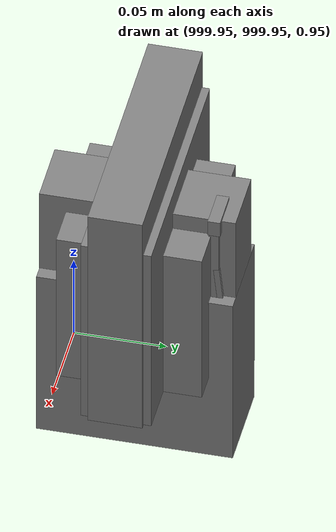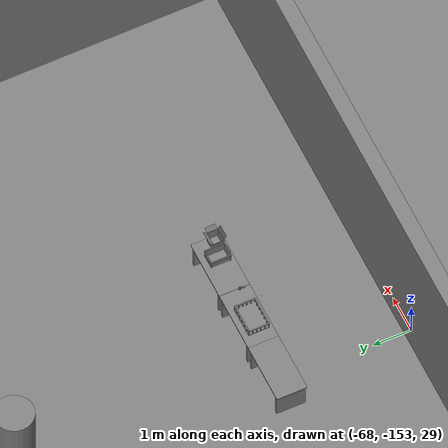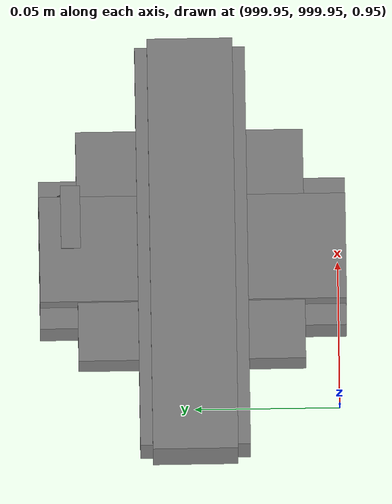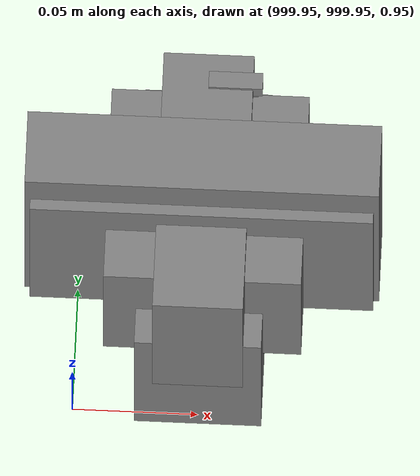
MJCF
<mujoco>
    <option gravity="0.000000000 0.000000000 -9.810000420" timestep="0.0049999999" integrator="implicitfast" density="1.225" viscosity="1.8000001e-05" noslip_iterations="10" iterations="100" sdf_iterations="50">
        <flag multiccd="disable"/>
    </option>
    <size memory="1000M"/>
    <compiler coordinate="local"/>
    <worldbody>
        <light cutoff="30" pos="0 1 1" dir="0 -1 -2"/>
        <light cutoff="30" pos="0 -1 1" dir="0 1 -2"/>
        <body pos="-64.866622925 -149.383972168 30.183746338" euler="89.999984741 89.999946594 0.000000000" name="openloong_gripper_2f85_fix_base_usda_bluebox_01">
            <geom contype="1" conaffinity="1" density="1000" type="box" material="" rgba="0.500000000 0.500000000 0.500000000 1.000000000" solimp="0.899999976 0.949999988 0.001000000" friction="1.000000000 0.005000000 0.000100000" solref="0.020000000 1.000000000" margin="0" condim="3" group="0" pos="0.276580811 0.187225342 0.000068665" quat="0.707106948 0.000077471 0.707106352 0.000077486" size="0.100000001 0.057999998 0.010000000" name="openloong_gripper_2f85_fix_base_usda_geom_40D1EACD_513C_476E_AEEA_4DF667C75590"/>
            <geom contype="1" conaffinity="1" density="1000" type="box" material="" rgba="0.500000000 0.500000000 0.500000000 1.000000000" solimp="0.899999976 0.949999988 0.001000000" friction="1.000000000 0.005000000 0.000100000" solref="0.020000000 1.000000000" margin="0" condim="3" group="0" pos="0.000000000 0.002883911 0.000000000" quat="0.999999881 0.000000000 0.000000000 0.000000000" size="0.254000008 0.003000000 0.172000006" name="openloong_gripper_2f85_fix_base_usda_geom_1A50C2B7_493B_40DB_BC93_6E1B12433A99"/>
            <geom contype="1" conaffinity="1" density="1000" type="box" material="" rgba="0.500000000 0.500000000 0.500000000 1.000000000" solimp="0.899999976 0.949999988 0.001000000" friction="1.000000000 0.005000000 0.000100000" solref="0.020000000 1.000000000" margin="0" condim="3" group="0" pos="0.000000000 0.124874115 0.173484802" quat="0.999796331 0.020176515 -0.000000015 0.000000030" size="0.259999990 0.119999997 0.007000000" name="openloong_gripper_2f85_fix_base_usda_geom_1E1AD202_FDF4_4715_B5D5_B31E4A72B23F"/>
            <geom contype="1" conaffinity="1" density="1000" type="box" material="" rgba="0.500000000 0.500000000 0.500000000 1.000000000" solimp="0.899999976 0.949999988 0.001000000" friction="1.000000000 0.005000000 0.000100000" solref="0.020000000 1.000000000" margin="0" condim="3" group="0" pos="0.000000000 0.124874115 -0.173469543" quat="0.999796331 -0.020176545 -0.000000015 0.000000000" size="0.259999990 0.119999997 0.007000000" name="openloong_gripper_2f85_fix_base_usda_geom_BDC14CC6_F6CB_40ED_ABED_118E5F71A2EF"/>
            <geom contype="1" conaffinity="1" density="1000" type="box" material="" rgba="0.500000000 0.500000000 0.500000000 1.000000000" solimp="0.899999976 0.949999988 0.001000000" friction="1.000000000 0.005000000 0.000100000" solref="0.020000000 1.000000000" margin="0" condim="3" group="0" pos="0.000000000 0.214008331 0.188980103" quat="0.999912977 0.013176724 0.000000015 0.000000000" size="0.259999990 0.029999999 0.012500000" name="openloong_gripper_2f85_fix_base_usda_geom_EA6DC2A7_AAAD_45DF_B12F_FDB9B66CD8E0"/>
            <geom contype="1" conaffinity="1" density="1000" type="box" material="" rgba="0.500000000 0.500000000 0.500000000 1.000000000" solimp="0.899999976 0.949999988 0.001000000" friction="1.000000000 0.005000000 0.000100000" solref="0.020000000 1.000000000" margin="0" condim="3" group="0" pos="-0.258361816 0.125289917 0.001876831" quat="0.702796936 -0.020792112 0.710783124 0.020769298" size="0.189999998 0.119999997 0.009000000" name="openloong_gripper_2f85_fix_base_usda_geom_5A54AB9E_586F_4C0E_9508_9BE2F3C1C2EA"/>
            <geom contype="1" conaffinity="1" density="1000" type="box" material="" rgba="0.500000000 0.500000000 0.500000000 1.000000000" solimp="0.899999976 0.949999988 0.001000000" friction="1.000000000 0.005000000 0.000100000" solref="0.020000000 1.000000000" margin="0" condim="3" group="0" pos="0.000000000 0.214008331 -0.188980103" quat="0.999912977 -0.013176769 0.000000030 0.000000015" size="0.259999990 0.029999999 0.012500000" name="openloong_gripper_2f85_fix_base_usda_geom_617A8285_BAA2_4137_98B4_8707867EA59E"/>
            <geom contype="1" conaffinity="1" density="1000" type="box" material="" rgba="0.500000000 0.500000000 0.500000000 1.000000000" solimp="0.899999976 0.949999988 0.001000000" friction="1.000000000 0.005000000 0.000100000" solref="0.020000000 1.000000000" margin="0" condim="3" group="0" pos="-0.276611328 0.187225342 0.000068665" quat="0.707106650 0.000077441 0.707106709 0.000077456" size="0.100000001 0.057999998 0.010000000" name="openloong_gripper_2f85_fix_base_usda_geom_40A11526_FEC5_410C_8723_09CFDC58D293"/>
            <geom contype="1" conaffinity="1" density="1000" type="box" material="" rgba="0.500000000 0.500000000 0.500000000 1.000000000" solimp="0.899999976 0.949999988 0.001000000" friction="1.000000000 0.005000000 0.000100000" solref="0.020000000 1.000000000" margin="0" condim="3" group="0" pos="0.258331299 0.125289917 0.001876831" quat="0.702851415 0.018856421 0.710823774 -0.019329369" size="0.189999998 0.119999997 0.009000000" name="openloong_gripper_2f85_fix_base_usda_geom_26E6207A_8F8C_4ED7_A54A_E135AE7156DA"/>
            <freejoint name="openloong_gripper_2f85_fix_base_usda_bluebox_01_joint"/>
            <site size="0.005000000 0.005000000 0.005000000" rgba="0.500000000 0.500000000 0.500000000 1.000000000" pos="0.000000000 0.000000000 0.000000000" quat="0.999961913 0.008726534 0.000000000 0.000000000" group="0" type="sphere" name="openloong_gripper_2f85_fix_base_usda_bluebox_01site"/>
        </body>
        <body pos="-64.496299744 -149.491867065 30.235729218" euler="0.000000000 0.000000000 89.999946594" name="openloong_gripper_2f85_fix_base_usda_cardboardbox_01">
            <geom contype="1" conaffinity="1" density="1000" type="box" material="" rgba="0.500000000 0.500000000 0.500000000 1.000000000" solimp="0.899999976 0.949999988 0.001000000" friction="1.000000000 0.005000000 0.000100000" solref="0.020000000 1.000000000" margin="0" condim="3" group="0" pos="-0.003166199 -0.004086494 0.005052090" quat="1.000000000 0.000000000 0.000000000 0.000000000" size="0.142499998 0.177500010 0.005000000" name="openloong_gripper_2f85_fix_base_usda_geom_4E62C17B_C6EC_4610_BFAD_E5D8BD49B0F9"/>
            <geom contype="1" conaffinity="1" density="1000" type="box" material="" rgba="0.500000000 0.500000000 0.500000000 1.000000000" solimp="0.899999976 0.949999988 0.001000000" friction="1.000000000 0.005000000 0.000100000" solref="0.020000000 1.000000000" margin="0" condim="3" group="0" pos="-0.003166199 0.170316696 0.150570869" quat="1.000000000 0.000000000 0.000000000 0.000000000" size="0.142499998 0.005000000 0.149999991" name="openloong_gripper_2f85_fix_base_usda_geom_CFF42F9B_D978_41BF_9946_A2CDD0E35045"/>
            <geom contype="1" conaffinity="1" density="1000" type="box" material="" rgba="0.500000000 0.500000000 0.500000000 1.000000000" solimp="0.899999976 0.949999988 0.001000000" friction="1.000000000 0.005000000 0.000100000" solref="0.020000000 1.000000000" margin="0" condim="3" group="0" pos="-0.147399902 -0.005307198 0.150570869" quat="1.000000000 0.000000000 0.000000000 0.000000000" size="0.005000000 0.177500010 0.149999991" name="openloong_gripper_2f85_fix_base_usda_geom_650CC896_FFA9_4B2D_A436_845D45E20DCB"/>
            <geom contype="1" conaffinity="1" density="1000" type="box" material="" rgba="0.500000000 0.500000000 0.500000000 1.000000000" solimp="0.899999976 0.949999988 0.001000000" friction="1.000000000 0.005000000 0.000100000" solref="0.020000000 1.000000000" margin="0" condim="3" group="0" pos="0.140275955 -0.005307198 0.150570869" quat="1.000000000 0.000000000 0.000000000 0.000000000" size="0.005000000 0.177500010 0.149999991" name="openloong_gripper_2f85_fix_base_usda_geom_F4FD9069_CD5F_46E8_ABDB_77A13AEC7489"/>
            <geom contype="1" conaffinity="1" density="1000" type="box" material="" rgba="0.500000000 0.500000000 0.500000000 1.000000000" solimp="0.899999976 0.949999988 0.001000000" friction="1.000000000 0.005000000 0.000100000" solref="0.020000000 1.000000000" margin="0" condim="3" group="0" pos="-0.003166199 -0.181550980 0.150570869" quat="1.000000000 0.000000000 0.000000000 0.000000000" size="0.142499998 0.005000000 0.149999991" name="openloong_gripper_2f85_fix_base_usda_geom_9D49A672_DC28_4795_8E2B_CF388018707B"/>
            <freejoint name="openloong_gripper_2f85_fix_base_usda_cardboardbox_01_joint"/>
            <site size="0.005000000 0.005000000 0.005000000" rgba="0.500000000 0.500000000 0.500000000 1.000000000" pos="0.000000000 0.000000000 0.000000000" quat="0.999961913 0.008726535 0.000000000 0.000000000" group="0" type="sphere" name="openloong_gripper_2f85_fix_base_usda_site_17EE7028_074D_4810_9C51_C032EE5B0B60"/>
            <body pos="0.139160156 -0.004048347 0.301930904" euler="-179.999954224 49.383502960 179.999954224" name="openloong_gripper_2f85_fix_base_usda_A1_006">
                <geom contype="1" conaffinity="1" density="1000" type="box" material="" rgba="0.500000000 0.500000000 0.500000000 1.000000000" solimp="0.899999976 0.949999988 0.001000000" friction="1.000000000 0.005000000 0.000100000" solref="0.020000000 1.000000000" margin="0" condim="3" group="0" pos="-0.071587563 0.000009537 0.001745224" quat="0.999999881 0.000000000 0.000000000 0.000000000" size="0.071249999 0.179999992 0.002500000" name="openloong_gripper_2f85_fix_base_usda_geom_1C0FAE43_6F4F_40B9_A684_8A54F5DDA85C"/>
                <joint armature="0" stiffness="0.07" damping="0.0099999998" axis="0.000000 1.000000 0.000000" type="hinge" name="openloong_gripper_2f85_fix_base_usda_A1_006"/>
            </body>
            <body pos="-0.145902634 -0.004086494 0.301938057" euler="-180.000000000 -60.000011444 -180.000000000" name="openloong_gripper_2f85_fix_base_usda_A2_006">
                <geom contype="1" conaffinity="1" density="1000" type="box" material="" rgba="0.500000000 0.500000000 0.500000000 1.000000000" solimp="0.899999976 0.949999988 0.001000000" friction="1.000000000 0.005000000 0.000100000" solref="0.020000000 1.000000000" margin="0" condim="3" group="0" pos="0.071268082 0.000009537 0.002717972" quat="0.000002921 0.000000000 -0.000000030 0.999999881" size="0.071249999 0.179999992 0.002500000" name="openloong_gripper_2f85_fix_base_usda_geom_BE71846C_6DA9_4608_BDC8_DFDBCB2C34C6"/>
                <joint armature="0" stiffness="0.07" damping="0.0099999998" axis="0.000000 1.000000 0.000000" type="hinge" name="openloong_gripper_2f85_fix_base_usda_A2_006"/>
            </body>
            <body pos="-0.003385544 0.175991058 0.301930904" euler="-125.858116150 -0.000004561 0.000002331" name="openloong_gripper_2f85_fix_base_usda_B2_006">
                <geom contype="1" conaffinity="1" density="1000" type="box" material="" rgba="0.500000000 0.500000000 0.500000000 1.000000000" solimp="0.899999976 0.949999988 0.001000000" friction="1.000000000 0.005000000 0.000100000" solref="0.020000000 1.000000000" margin="0" condim="3" group="0" pos="0.000009537 -0.070939064 -0.002470016" quat="0.999614120 0.027776197 -0.000000015 0.000000030" size="0.137500003 0.064999998 0.005000000" name="openloong_gripper_2f85_fix_base_usda_geom_6076A9BF_C143_4F30_B097_5981453D5EA2"/>
                <joint armature="0" stiffness="0.07" damping="0.0099999998" axis="1.000000 0.000000 0.000000" type="hinge" name="openloong_gripper_2f85_fix_base_usda_B2_006"/>
            </body>
            <body pos="-0.003385544 -0.184140205 0.301938057" euler="147.805557251 0.000000000 0.000000000" name="openloong_gripper_2f85_fix_base_usda_B1_006">
                <geom contype="1" conaffinity="1" density="1000" type="box" material="" rgba="0.500000000 0.500000000 0.500000000 1.000000000" solimp="0.899999976 0.949999988 0.001000000" friction="1.000000000 0.005000000 0.000100000" solref="0.020000000 1.000000000" margin="0" condim="3" group="0" pos="-0.000028610 0.070202351 -0.002703667" quat="0.999614179 -0.027776167 0.000000000 0.000000000" size="0.137500003 0.064999998 0.005000000" name="openloong_gripper_2f85_fix_base_usda_geom_14A19E7D_0D81_403A_BB93_FA47438542BB"/>
                <joint armature="0" stiffness="0.07" damping="0.0099999998" axis="1.000000 0.000000 0.000000" type="hinge" name="openloong_gripper_2f85_fix_base_usda_B1_006"/>
            </body>
        </body>
        <body pos="-65.882858276 -149.481979370 30.229999542" euler="-64.487716675 0.000000000 0.000000000" name="openloong_gripper_2f85_fix_base_usda_Barcode">
            <geom contype="1" conaffinity="1" density="1000" type="box" material="" rgba="0.500000000 0.500000000 0.500000000 1.000000000" solimp="0.899999976 0.949999988 0.001000000" friction="1.000000000 0.005000000 0.000100000" solref="0.020000000 1.000000000" margin="0" condim="3" group="0" pos="0.000000000 0.013038635 0.001419067" quat="0.000000000 0.000000000 0.000000000 1.000000119" size="0.034000002 0.010000000 0.017999999" name="openloong_gripper_2f85_fix_base_usda_geom_ED38F8AD_5099_4065_8651_507E46A93C47"/>
            <geom contype="1" conaffinity="1" density="1000" type="box" material="" rgba="0.500000000 0.500000000 0.500000000 1.000000000" solimp="0.899999976 0.949999988 0.001000000" friction="1.000000000 0.005000000 0.000100000" solref="0.020000000 1.000000000" margin="0" condim="3" group="0" pos="0.000000000 -0.035301208 -0.007095337" quat="0.000000000 0.000000000 -0.043619365 0.999048233" size="0.028999999 0.010000000 0.020000000" name="openloong_gripper_2f85_fix_base_usda_geom_0EF75705_78C4_46AE_9A84_59F357105CAB"/>
            <geom contype="1" conaffinity="1" density="1000" type="box" material="" rgba="0.500000000 0.500000000 0.500000000 1.000000000" solimp="0.899999976 0.949999988 0.001000000" friction="1.000000000 0.005000000 0.000100000" solref="0.020000000 1.000000000" margin="0" condim="3" group="0" pos="0.000000000 -0.043411255 -0.011749268" quat="0.922262907 0.386563420 0.000000000 0.000000000" size="0.026000001 0.010000000 0.020000000" name="openloong_gripper_2f85_fix_base_usda_geom_BA51552A_64CD_4A98_B628_9003E89930DF"/>
            <geom contype="1" conaffinity="1" density="1000" type="box" material="" rgba="0.500000000 0.500000000 0.500000000 1.000000000" solimp="0.899999976 0.949999988 0.001000000" friction="1.000000000 0.005000000 0.000100000" solref="0.020000000 1.000000000" margin="0" condim="3" group="0" pos="0.000000000 -0.016967773 -0.031860352" quat="0.000000000 0.000000000 0.000000000 1.000000119" size="0.008000000 0.010000000 0.013000000" name="openloong_gripper_2f85_fix_base_usda_geom_54C0229D_1CE0_44C6_90AF_913B70F4BFE3"/>
            <geom contype="1" conaffinity="1" density="1000" type="box" material="" rgba="0.500000000 0.500000000 0.500000000 1.000000000" solimp="0.899999976 0.949999988 0.001000000" friction="1.000000000 0.005000000 0.000100000" solref="0.020000000 1.000000000" margin="0" condim="3" group="0" pos="0.000000000 -0.001869202 0.000312805" quat="0.953716993 0.300705761 0.000000000 0.000000000" size="0.032000002 0.010000000 0.018999999" name="openloong_gripper_2f85_fix_base_usda_geom_BEBA702F_9607_4653_8BEE_4A607820C04E"/>
            <geom contype="1" conaffinity="1" density="1000" type="box" material="" rgba="0.500000000 0.500000000 0.500000000 1.000000000" solimp="0.899999976 0.949999988 0.001000000" friction="1.000000000 0.005000000 0.000100000" solref="0.020000000 1.000000000" margin="0" condim="3" group="0" pos="0.000000000 -0.019531250 -0.003173828" quat="0.953716993 0.300705761 0.000000000 0.000000000" size="0.030999999 0.010000000 0.020000000" name="openloong_gripper_2f85_fix_base_usda_geom_A1091F3A_883B_4F6C_A949_0007A2FD8432"/>
            <geom contype="1" conaffinity="1" density="1000" type="box" material="" rgba="0.500000000 0.500000000 0.500000000 1.000000000" solimp="0.899999976 0.949999988 0.001000000" friction="1.000000000 0.005000000 0.000100000" solref="0.020000000 1.000000000" margin="0" condim="3" group="0" pos="0.000000000 -0.035301208 -0.007095337" quat="0.953716993 0.300705761 0.000000000 0.000000000" size="0.028999999 0.010000000 0.020000000" name="openloong_gripper_2f85_fix_base_usda_geom_8A92614F_43D7_4486_82B4_8A6E20D9CF68"/>
            <geom contype="1" conaffinity="1" density="1000" type="box" material="" rgba="0.500000000 0.500000000 0.500000000 1.000000000" solimp="0.899999976 0.949999988 0.001000000" friction="1.000000000 0.005000000 0.000100000" solref="0.020000000 1.000000000" margin="0" condim="3" group="0" pos="0.000000000 -0.042617798 -0.071121216" quat="0.000000000 0.000000000 0.000000000 1.000000119" size="0.013000000 0.021000000 0.059999999" name="openloong_gripper_2f85_fix_base_usda_geom_A3F5DA1F_8514_4A00_BB59_141A076A009E"/>
            <freejoint name="openloong_gripper_2f85_fix_base_usda_Barcode_joint"/>
            <site size="0.005000000 0.005000000 0.005000000" rgba="0.500000000 0.500000000 0.500000000 1.000000000" pos="0.000000000 0.000000000 0.000000000" quat="1.000000000 0.000000000 0.000000000 0.000000000" group="0" type="sphere" name="openloong_gripper_2f85_fix_base_usda_Barcode_site"/>
        </body>
        <body pos="-66.745018005 -149.392349243 30.184000015" euler="0.000000000 0.000000000 89.999946594" name="[22329918491174]_Basket_01">
            <geom contype="1" conaffinity="1" density="1000" type="box" material="" rgba="0.500000000 0.500000000 0.500000000 1.000000000" solimp="0.899999976 0.949999988 0.001000000" friction="1.000000000 0.005000000 0.000100000" solref="0.020000000 1.000000000" margin="0" condim="3" group="0" pos="-0.052425385 0.389207840 0.089787483" quat="0.707107008 0.000000000 0.000000000 0.707106411" size="0.014249999 0.014249999 0.059999999" name="[22329918491174]_geom_A40F0653_0BFD_4647_A580_391540113171"/>
            <geom contype="1" conaffinity="1" density="1000" type="box" material="" rgba="0.500000000 0.500000000 0.500000000 1.000000000" solimp="0.899999976 0.949999988 0.001000000" friction="1.000000000 0.005000000 0.000100000" solref="0.020000000 1.000000000" margin="0" condim="3" group="0" pos="0.264015198 -0.133043289 0.089787483" quat="0.707107008 0.000000000 0.000000000 0.707106411" size="0.014249999 0.014249999 0.059999999" name="[22329918491174]_geom_EAED1F03_6FF7_4AB0_BA6A_F1C824489B32"/>
            <geom contype="1" conaffinity="1" density="1000" type="box" material="" rgba="0.500000000 0.500000000 0.500000000 1.000000000" solimp="0.899999976 0.949999988 0.001000000" friction="1.000000000 0.005000000 0.000100000" solref="0.020000000 1.000000000" margin="0" condim="3" group="0" pos="-0.264015198 -0.265548706 0.089793205" quat="0.707107008 0.000000000 0.000000000 0.707106411" size="0.014249999 0.014249999 0.059999999" name="[22329918491174]_geom_BDFDA203_FA16_457A_AC14_E3929F9F3370"/>
            <geom contype="1" conaffinity="1" density="1000" type="box" material="" rgba="0.500000000 0.500000000 0.500000000 1.000000000" solimp="0.899999976 0.949999988 0.001000000" friction="1.000000000 0.005000000 0.000100000" solref="0.020000000 1.000000000" margin="0" condim="3" group="0" pos="-0.160263062 -0.389322281 0.089793205" quat="0.707107008 0.000000000 0.000000000 0.707106411" size="0.014249999 0.014249999 0.059999999" name="[22329918491174]_geom_6FA5D6D9_6D1C_4ECF_82EC_7925946A1206"/>
            <geom contype="1" conaffinity="1" density="1000" type="box" material="" rgba="0.500000000 0.500000000 0.500000000 1.000000000" solimp="0.899999976 0.949999988 0.001000000" friction="1.000000000 0.005000000 0.000100000" solref="0.020000000 1.000000000" margin="0" condim="3" group="0" pos="0.162265778 -0.389322281 0.089787483" quat="0.707107008 0.000000000 0.000000000 0.707106411" size="0.014249999 0.014249999 0.059999999" name="[22329918491174]_geom_2B48A52D_7C89_4512_B7A8_7DBBD4E3D79B"/>
            <geom contype="1" conaffinity="1" density="1000" type="box" material="" rgba="0.500000000 0.500000000 0.500000000 1.000000000" solimp="0.899999976 0.949999988 0.001000000" friction="1.000000000 0.005000000 0.000100000" solref="0.020000000 1.000000000" margin="0" condim="3" group="0" pos="0.264015198 0.389207840 0.089787483" quat="0.707107008 0.000000000 0.000000000 0.707106411" size="0.014249999 0.014249999 0.059999999" name="[22329918491174]_geom_F75BCCA3_903C_4496_9FEA_2C0891A295A6"/>
            <geom contype="1" conaffinity="1" density="1000" type="box" material="" rgba="0.500000000 0.500000000 0.500000000 1.000000000" solimp="0.899999976 0.949999988 0.001000000" friction="1.000000000 0.005000000 0.000100000" solref="0.020000000 1.000000000" margin="0" condim="3" group="0" pos="-0.264015198 -0.133043289 0.089793205" quat="0.707107008 0.000000000 0.000000000 0.707106411" size="0.014249999 0.014249999 0.059999999" name="[22329918491174]_geom_67A43322_79D3_4D5D_BC33_ECCEA6E5581B"/>
            <geom contype="1" conaffinity="1" density="1000" type="box" material="" rgba="0.500000000 0.500000000 0.500000000 1.000000000" solimp="0.899999976 0.949999988 0.001000000" friction="1.000000000 0.005000000 0.000100000" solref="0.020000000 1.000000000" margin="0" condim="3" group="0" pos="-0.264026642 0.269256592 0.089793205" quat="0.707107008 0.000000000 0.000000000 0.707106411" size="0.014249999 0.014249999 0.059999999" name="[22329918491174]_geom_3CFD1726_0F1C_494D_8BE8_FA0EDA764E14"/>
            <geom contype="1" conaffinity="1" density="1000" type="box" material="" rgba="0.500000000 0.500000000 0.500000000 1.000000000" solimp="0.899999976 0.949999988 0.001000000" friction="1.000000000 0.005000000 0.000100000" solref="0.020000000 1.000000000" margin="0" condim="3" group="0" pos="0.054462433 0.389207840 0.089787483" quat="0.707107008 0.000000000 0.000000000 0.707106411" size="0.014249999 0.014249999 0.059999999" name="[22329918491174]_geom_0964BFD3_5721_497C_B866_74CA4E8FDAC7"/>
            <geom contype="1" conaffinity="1" density="1000" type="box" material="" rgba="0.500000000 0.500000000 0.500000000 1.000000000" solimp="0.899999976 0.949999988 0.001000000" friction="1.000000000 0.005000000 0.000100000" solref="0.020000000 1.000000000" margin="0" condim="3" group="0" pos="0.054462433 -0.389322281 0.089787483" quat="0.707107008 0.000000000 0.000000000 0.707106411" size="0.014249999 0.014249999 0.059999999" name="[22329918491174]_geom_4EB90F01_1AE5_43E6_A184_3392AFF8537A"/>
            <geom contype="1" conaffinity="1" density="1000" type="box" material="" rgba="0.500000000 0.500000000 0.500000000 1.000000000" solimp="0.899999976 0.949999988 0.001000000" friction="1.000000000 0.005000000 0.000100000" solref="0.020000000 1.000000000" margin="0" condim="3" group="0" pos="0.264015198 0.269256592 0.089793205" quat="0.707107008 0.000000000 0.000000000 0.707106411" size="0.014249999 0.014249999 0.059999999" name="[22329918491174]_geom_45C0D45B_59A7_481C_A173_BD8E6308962B"/>
            <geom contype="1" conaffinity="1" density="1000" type="box" material="" rgba="0.500000000 0.500000000 0.500000000 1.000000000" solimp="0.899999976 0.949999988 0.001000000" friction="1.000000000 0.005000000 0.000100000" solref="0.020000000 1.000000000" margin="0" condim="3" group="0" pos="0.264015198 -0.389322281 0.089787483" quat="0.707107008 0.000000000 0.000000000 0.707106411" size="0.014249999 0.014249999 0.059999999" name="[22329918491174]_geom_889DA0BC_B22F_4C14_93CD_C536661FFCD2"/>
            <geom contype="1" conaffinity="1" density="1000" type="box" material="" rgba="0.500000000 0.500000000 0.500000000 1.000000000" solimp="0.899999976 0.949999988 0.001000000" friction="1.000000000 0.005000000 0.000100000" solref="0.020000000 1.000000000" margin="0" condim="3" group="0" pos="0.000000000 0.000000000 0.015998840" quat="0.707107008 0.000000000 0.000000000 0.707106411" size="0.403499991 0.279000014 0.015750000" name="[22329918491174]_geom_0FF08FAE_9E7E_4755_97BC_6B4113BF3776"/>
            <geom contype="1" conaffinity="1" density="1000" type="box" material="" rgba="0.500000000 0.500000000 0.500000000 1.000000000" solimp="0.899999976 0.949999988 0.001000000" friction="1.000000000 0.005000000 0.000100000" solref="0.020000000 1.000000000" margin="0" condim="3" group="0" pos="0.000000000 -0.389476776 0.163619041" quat="0.707107008 0.000000000 0.000000000 0.707106411" size="0.015000000 0.277500004 0.015750000" name="[22329918491174]_geom_A80F2296_CABA_467A_9B5E_3F0105C1CA71"/>
            <geom contype="1" conaffinity="1" density="1000" type="box" material="" rgba="0.500000000 0.500000000 0.500000000 1.000000000" solimp="0.899999976 0.949999988 0.001000000" friction="1.000000000 0.005000000 0.000100000" solref="0.020000000 1.000000000" margin="0" condim="3" group="0" pos="0.162265778 0.389207840 0.089787483" quat="0.707107008 0.000000000 0.000000000 0.707106411" size="0.014249999 0.014249999 0.059999999" name="[22329918491174]_geom_3E896A17_4BED_47ED_A8D2_7E60A7C91A17"/>
            <geom contype="1" conaffinity="1" density="1000" type="box" material="" rgba="0.500000000 0.500000000 0.500000000 1.000000000" solimp="0.899999976 0.949999988 0.001000000" friction="1.000000000 0.005000000 0.000100000" solref="0.020000000 1.000000000" margin="0" condim="3" group="0" pos="0.000000000 0.389471054 0.163619041" quat="0.707107008 0.000000000 0.000000000 0.707106411" size="0.015000000 0.277500004 0.015750000" name="[22329918491174]_geom_03B5B331_A9A1_4715_9DD8_68A6C5F964E1"/>
            <geom contype="1" conaffinity="1" density="1000" type="box" material="" rgba="0.500000000 0.500000000 0.500000000 1.000000000" solimp="0.899999976 0.949999988 0.001000000" friction="1.000000000 0.005000000 0.000100000" solref="0.020000000 1.000000000" margin="0" condim="3" group="0" pos="-0.263511658 0.000000000 0.163619041" quat="0.707107008 0.000000000 0.000000000 0.707106411" size="0.403499991 0.015000000 0.015750000" name="[22329918491174]_geom_E053CEB4_771F_421D_ADDE_004C42434D43"/>
            <geom contype="1" conaffinity="1" density="1000" type="box" material="" rgba="0.500000000 0.500000000 0.500000000 1.000000000" solimp="0.899999976 0.949999988 0.001000000" friction="1.000000000 0.005000000 0.000100000" solref="0.020000000 1.000000000" margin="0" condim="3" group="0" pos="-0.264015198 0.141334534 0.089793205" quat="0.707107008 0.000000000 0.000000000 0.707106411" size="0.014249999 0.014249999 0.059999999" name="[22329918491174]_geom_2F8362DF_B58A_4ABB_A90A_580C61E23B44"/>
            <geom contype="1" conaffinity="1" density="1000" type="box" material="" rgba="0.500000000 0.500000000 0.500000000 1.000000000" solimp="0.899999976 0.949999988 0.001000000" friction="1.000000000 0.005000000 0.000100000" solref="0.020000000 1.000000000" margin="0" condim="3" group="0" pos="0.264015198 -0.265548706 0.089787483" quat="0.707107008 0.000000000 0.000000000 0.707106411" size="0.014249999 0.014249999 0.059999999" name="[22329918491174]_geom_8C4A3B27_01B6_421A_8914_1E7B5A06D528"/>
            <geom contype="1" conaffinity="1" density="1000" type="box" material="" rgba="0.500000000 0.500000000 0.500000000 1.000000000" solimp="0.899999976 0.949999988 0.001000000" friction="1.000000000 0.005000000 0.000100000" solref="0.020000000 1.000000000" margin="0" condim="3" group="0" pos="-0.160263062 0.389207840 0.089787483" quat="0.707107008 0.000000000 0.000000000 0.707106411" size="0.014249999 0.014249999 0.059999999" name="[22329918491174]_geom_1C4F1388_D93A_4BE0_9A48_A17EDF88CEE9"/>
            <geom contype="1" conaffinity="1" density="1000" type="box" material="" rgba="0.500000000 0.500000000 0.500000000 1.000000000" solimp="0.899999976 0.949999988 0.001000000" friction="1.000000000 0.005000000 0.000100000" solref="0.020000000 1.000000000" margin="0" condim="3" group="0" pos="-0.052425385 -0.389322281 0.089787483" quat="0.707107008 0.000000000 0.000000000 0.707106411" size="0.014249999 0.014249999 0.059999999" name="[22329918491174]_geom_E99215CE_6D41_4994_B032_92610FBD1A29"/>
            <geom contype="1" conaffinity="1" density="1000" type="box" material="" rgba="0.500000000 0.500000000 0.500000000 1.000000000" solimp="0.899999976 0.949999988 0.001000000" friction="1.000000000 0.005000000 0.000100000" solref="0.020000000 1.000000000" margin="0" condim="3" group="0" pos="-0.264026642 -0.389322281 0.089793205" quat="0.707107008 0.000000000 0.000000000 0.707106411" size="0.014249999 0.014249999 0.059999999" name="[22329918491174]_geom_404DBAAA_C4BB_40A5_91AD_6FE104539C4C"/>
            <geom contype="1" conaffinity="1" density="1000" type="box" material="" rgba="0.500000000 0.500000000 0.500000000 1.000000000" solimp="0.899999976 0.949999988 0.001000000" friction="1.000000000 0.005000000 0.000100000" solref="0.020000000 1.000000000" margin="0" condim="3" group="0" pos="0.264015198 0.141334534 0.089787483" quat="0.707107008 0.000000000 0.000000000 0.707106411" size="0.014249999 0.014249999 0.059999999" name="[22329918491174]_geom_485CEBE8_58C0_4706_A272_4615DD162F88"/>
            <geom contype="1" conaffinity="1" density="1000" type="box" material="" rgba="0.500000000 0.500000000 0.500000000 1.000000000" solimp="0.899999976 0.949999988 0.001000000" friction="1.000000000 0.005000000 0.000100000" solref="0.020000000 1.000000000" margin="0" condim="3" group="0" pos="-0.264015198 0.389207840 0.089793205" quat="0.707107008 0.000000000 0.000000000 0.707106411" size="0.014249999 0.014249999 0.059999999" name="[22329918491174]_geom_8725711C_95FC_48B9_9053_CC5464D15DD5"/>
            <geom contype="1" conaffinity="1" density="1000" type="box" material="" rgba="0.500000000 0.500000000 0.500000000 1.000000000" solimp="0.899999976 0.949999988 0.001000000" friction="1.000000000 0.005000000 0.000100000" solref="0.020000000 1.000000000" margin="0" condim="3" group="0" pos="0.264015198 0.004480362 0.089787483" quat="0.707107008 0.000000000 0.000000000 0.707106411" size="0.014249999 0.014249999 0.059999999" name="[22329918491174]_geom_608207FC_3C99_4306_9C1A_311D8B597D84"/>
            <geom contype="1" conaffinity="1" density="1000" type="box" material="" rgba="0.500000000 0.500000000 0.500000000 1.000000000" solimp="0.899999976 0.949999988 0.001000000" friction="1.000000000 0.005000000 0.000100000" solref="0.020000000 1.000000000" margin="0" condim="3" group="0" pos="0.263694763 -0.000011444 0.163619041" quat="0.707107008 0.000000000 0.000000000 0.707106411" size="0.403499991 0.015000000 0.015750000" name="[22329918491174]_geom_0123795F_B207_4D06_BE60_0B1032255AC1"/>
            <geom contype="1" conaffinity="1" density="1000" type="box" material="" rgba="0.500000000 0.500000000 0.500000000 1.000000000" solimp="0.899999976 0.949999988 0.001000000" friction="1.000000000 0.005000000 0.000100000" solref="0.020000000 1.000000000" margin="0" condim="3" group="0" pos="-0.264015198 0.004480362 0.089793205" quat="0.707107008 0.000000000 0.000000000 0.707106411" size="0.014249999 0.014249999 0.059999999" name="[22329918491174]_geom_3D01F201_2F37_4E33_908A_8632B2938AAD"/>
            <freejoint name="[22329918491174]_joint_E5075E22_E86D_417A_B27B_DE232B78DF2D"/>
        </body>
        <body pos="0.000000000 0.000000000 0.000000000" euler="0.000000000 0.000000000 0.000000000" name="Static Objects_Static Objects">
            <geom contype="1" conaffinity="1" density="1000" type="box" material="" rgba="0.500000000 0.500000000 0.500000000 1.000000000" solimp="0.899999976 0.949999988 0.001000000" friction="1.000000000 0.005000000 0.000100000" solref="0.020000000 1.000000000" margin="0" condim="3" group="0" pos="-67.544113159 -149.365814209 29.727830887" quat="0.500000417 0.499999970 0.499999553 0.499999970" size="0.381000012 0.319999993 0.041000001" name="Static Objects_geom_5FE33716_A7D0_4E0C_B570_428B61C9BE81"/>
            <geom contype="1" conaffinity="1" density="1000" type="box" material="" rgba="0.500000000 0.500000000 0.500000000 1.000000000" solimp="0.899999976 0.949999988 0.001000000" friction="1.000000000 0.005000000 0.000100000" solref="0.020000000 1.000000000" margin="0" condim="3" group="0" pos="-68.239501953 -149.365814209 30.086868286" quat="0.500000417 0.499999970 0.499999553 0.499999970" size="0.370999992 0.039500002 0.745000005" name="Static Objects_geom_54C54213_8319_4879_A09B_952EFE473B8A"/>
            <geom contype="1" conaffinity="1" density="1000" type="box" material="" rgba="0.500000000 0.500000000 0.500000000 1.000000000" solimp="0.899999976 0.949999988 0.001000000" friction="1.000000000 0.005000000 0.000100000" solref="0.020000000 1.000000000" margin="0" condim="3" group="0" pos="-68.239501953 -149.365814209 30.147235870" quat="0.500000417 0.499999970 0.499999553 0.499999970" size="0.400000006 0.022000000 0.800000012" name="Static Objects_geom_1518AB11_6976_41E1_9163_2B7D2532BAE5"/>
            <geom contype="1" conaffinity="1" density="1000" type="box" material="" rgba="0.500000000 0.500000000 0.500000000 1.000000000" solimp="0.899999976 0.949999988 0.001000000" friction="1.000000000 0.005000000 0.000100000" solref="0.020000000 1.000000000" margin="0" condim="3" group="0" pos="-68.934890747 -149.365814209 29.727830887" quat="0.500000417 0.499999970 0.499999553 0.499999970" size="0.381000012 0.319999993 0.041000001" name="Static Objects_geom_6C990861_DFF7_40B9_8CA1_0DDAEBA6B95A"/>
            <geom contype="1" conaffinity="1" density="1000" type="box" material="" rgba="0.500000000 0.500000000 0.500000000 1.000000000" solimp="0.899999976 0.949999988 0.001000000" friction="1.000000000 0.005000000 0.000100000" solref="0.020000000 1.000000000" margin="0" condim="3" group="0" pos="-68.239501953 -149.365814209 29.561563492" quat="0.500000417 0.499999970 0.499999553 0.499999970" size="0.020000000 0.022000000 0.660000026" name="Static Objects_geom_3C537B3C_F350_4A84_95D0_C9823ABFD2FF"/>
            <geom contype="1" conaffinity="1" density="1000" type="box" material="" rgba="0.500000000 0.500000000 0.500000000 1.000000000" solimp="0.899999976 0.949999988 0.001000000" friction="1.000000000 0.005000000 0.000100000" solref="0.020000000 1.000000000" margin="0" condim="3" group="0" pos="-65.945671082 -149.365814209 29.727830887" quat="0.500000417 0.499999970 0.499999553 0.499999970" size="0.381000012 0.319999993 0.041000001" name="Static Objects_geom_7B71C00E_A0DD_4AA5_B2EC_7332318ACAB2"/>
            <geom contype="1" conaffinity="1" density="1000" type="box" material="" rgba="0.500000000 0.500000000 0.500000000 1.000000000" solimp="0.899999976 0.949999988 0.001000000" friction="1.000000000 0.005000000 0.000100000" solref="0.020000000 1.000000000" margin="0" condim="3" group="0" pos="-66.641059875 -149.365814209 30.086868286" quat="0.500000417 0.499999970 0.499999553 0.499999970" size="0.370999992 0.039500002 0.745000005" name="Static Objects_geom_BBDE8202_9254_40B2_A967_B075CFC12B8A"/>
            <geom contype="1" conaffinity="1" density="1000" type="box" material="" rgba="0.500000000 0.500000000 0.500000000 1.000000000" solimp="0.899999976 0.949999988 0.001000000" friction="1.000000000 0.005000000 0.000100000" solref="0.020000000 1.000000000" margin="0" condim="3" group="0" pos="-66.641059875 -149.365814209 30.147235870" quat="0.500000417 0.499999970 0.499999553 0.499999970" size="0.400000006 0.022000000 0.800000012" name="Static Objects_geom_D527AD70_2B9E_4FA6_8541_F90DE5D48DB4"/>
            <geom contype="1" conaffinity="1" density="1000" type="box" material="" rgba="0.500000000 0.500000000 0.500000000 1.000000000" solimp="0.899999976 0.949999988 0.001000000" friction="1.000000000 0.005000000 0.000100000" solref="0.020000000 1.000000000" margin="0" condim="3" group="0" pos="-67.336448669 -149.365814209 29.727830887" quat="0.500000417 0.499999970 0.499999553 0.499999970" size="0.381000012 0.319999993 0.041000001" name="Static Objects_geom_5CBF3DD9_8D3E_424B_8337_776B9C38EF01"/>
            <geom contype="1" conaffinity="1" density="1000" type="box" material="" rgba="0.500000000 0.500000000 0.500000000 1.000000000" solimp="0.899999976 0.949999988 0.001000000" friction="1.000000000 0.005000000 0.000100000" solref="0.020000000 1.000000000" margin="0" condim="3" group="0" pos="-66.641059875 -149.365814209 29.561563492" quat="0.500000417 0.499999970 0.499999553 0.499999970" size="0.020000000 0.022000000 0.660000026" name="Static Objects_geom_97322825_FA6E_4E95_8FF0_03E17D8E80D3"/>
            <geom contype="1" conaffinity="1" density="1000" type="box" material="" rgba="0.500000000 0.500000000 0.500000000 1.000000000" solimp="0.899999976 0.949999988 0.001000000" friction="1.000000000 0.005000000 0.000100000" solref="0.020000000 1.000000000" margin="0" condim="3" group="0" pos="-64.338577271 -149.365814209 29.727830887" quat="0.500000417 0.499999970 0.499999553 0.499999970" size="0.381000012 0.319999993 0.041000001" name="Static Objects_geom_20DED057_ADE6_446A_8DAA_2EE8D95123EA"/>
            <geom contype="1" conaffinity="1" density="1000" type="box" material="" rgba="0.500000000 0.500000000 0.500000000 1.000000000" solimp="0.899999976 0.949999988 0.001000000" friction="1.000000000 0.005000000 0.000100000" solref="0.020000000 1.000000000" margin="0" condim="3" group="0" pos="-65.033966064 -149.365814209 30.086868286" quat="0.500000417 0.499999970 0.499999553 0.499999970" size="0.370999992 0.039500002 0.745000005" name="Static Objects_geom_C6535306_50D9_4281_A369_8BD6F860838A"/>
            <geom contype="1" conaffinity="1" density="1000" type="box" material="" rgba="0.500000000 0.500000000 0.500000000 1.000000000" solimp="0.899999976 0.949999988 0.001000000" friction="1.000000000 0.005000000 0.000100000" solref="0.020000000 1.000000000" margin="0" condim="3" group="0" pos="-65.033966064 -149.365814209 30.147235870" quat="0.500000417 0.499999970 0.499999553 0.499999970" size="0.400000006 0.022000000 0.800000012" name="Static Objects_geom_8F6921FF_27E7_462F_9171_A60AE1FD9DC8"/>
            <geom contype="1" conaffinity="1" density="1000" type="box" material="" rgba="0.500000000 0.500000000 0.500000000 1.000000000" solimp="0.899999976 0.949999988 0.001000000" friction="1.000000000 0.005000000 0.000100000" solref="0.020000000 1.000000000" margin="0" condim="3" group="0" pos="-65.729354858 -149.365814209 29.727830887" quat="0.500000417 0.499999970 0.499999553 0.499999970" size="0.381000012 0.319999993 0.041000001" name="Static Objects_geom_995E8989_94F0_4A7A_BDFF_A1A3EBDAB84B"/>
            <geom contype="1" conaffinity="1" density="1000" type="box" material="" rgba="0.500000000 0.500000000 0.500000000 1.000000000" solimp="0.899999976 0.949999988 0.001000000" friction="1.000000000 0.005000000 0.000100000" solref="0.020000000 1.000000000" margin="0" condim="3" group="0" pos="-65.033966064 -149.365814209 29.561563492" quat="0.500000417 0.499999970 0.499999553 0.499999970" size="0.020000000 0.022000000 0.660000026" name="Static Objects_geom_F0299EEA_D5F6_4CD7_978A_09C1856A3C9B"/>
            <geom contype="1" conaffinity="1" density="1000" type="box" material="" rgba="0.500000000 0.500000000 0.500000000 1.000000000" solimp="0.899999976 0.949999988 0.001000000" friction="1.000000000 0.005000000 0.000100000" solref="0.020000000 1.000000000" margin="0" condim="3" group="0" pos="-61.754566193 -137.853729248 33.906845093" quat="0.707107067 0.000000000 0.000000000 0.707106471" size="0.759999990 0.759999990 4.500000000" name="Static Objects_geom_77FFE98C_E45D_4AC3_B3F1_E80F68388F73"/>
            <geom contype="1" conaffinity="1" density="1000" type="box" material="" rgba="0.500000000 0.500000000 0.500000000 1.000000000" solimp="0.899999976 0.949999988 0.001000000" friction="1.000000000 0.005000000 0.000100000" solref="0.020000000 1.000000000" margin="0" condim="3" group="0" pos="-57.511135101 -144.927108765 31.707921982" quat="1.000000000 0.000000000 0.000000000 0.000000000" size="0.200000003 8.000000000 2.299999952" name="Static Objects_geom_8B3E0D4B_F766_44C1_AEEE_201CE94EE35E"/>
            <geom contype="1" conaffinity="1" density="1000" type="box" material="" rgba="0.500000000 0.500000000 0.500000000 1.000000000" solimp="0.899999976 0.949999988 0.001000000" friction="1.000000000 0.005000000 0.000100000" solref="0.020000000 1.000000000" margin="0" condim="3" group="0" pos="-80.517646790 -157.574050903 31.688196182" quat="0.707107067 0.000000000 0.000000000 0.707106471" size="0.600000024 0.600000024 2.299999952" name="Static Objects_geom_ED052932_1BFF_465D_B461_E54C2DEF729A"/>
            <geom contype="1" conaffinity="1" density="1000" type="box" material="" rgba="0.500000000 0.500000000 0.500000000 1.000000000" solimp="0.899999976 0.949999988 0.001000000" friction="1.000000000 0.005000000 0.000100000" solref="0.020000000 1.000000000" margin="0" condim="3" group="0" pos="-80.711044312 -147.414932251 31.666158676" quat="1.000000000 0.000000000 0.000000000 0.000000000" size="0.200000003 10.000000000 2.299999952" name="Static Objects_geom_9EFDC6A2_F168_43F9_BC16_D4B1CB8F5149"/>
            <geom contype="1" conaffinity="1" density="1000" type="box" material="" rgba="0.500000000 0.500000000 0.500000000 1.000000000" solimp="0.899999976 0.949999988 0.001000000" friction="1.000000000 0.005000000 0.000100000" solref="0.020000000 1.000000000" margin="0" condim="3" group="0" pos="-57.687217712 -137.434692383 31.688196182" quat="0.707107067 0.000000000 0.000000000 0.707106471" size="0.600000024 0.600000024 2.299999952" name="Static Objects_geom_2A81428F_E76A_4B50_84C4_72EFCBAD142A"/>
            <geom contype="1" conaffinity="1" density="1000" type="box" material="" rgba="0.500000000 0.500000000 0.500000000 1.000000000" solimp="0.899999976 0.949999988 0.001000000" friction="1.000000000 0.005000000 0.000100000" solref="0.020000000 1.000000000" margin="0" condim="3" group="0" pos="-69.537033081 -140.263229370 31.714921951" quat="0.707107067 0.000000000 0.000000000 0.707106471" size="0.759999990 4.500000000 2.299999952" name="Static Objects_geom_1F90E472_A6D5_4F2A_B921_D3CB86E97FE4"/>
            <geom contype="1" conaffinity="1" density="1000" type="box" material="" rgba="0.500000000 0.500000000 0.500000000 1.000000000" solimp="0.899999976 0.949999988 0.001000000" friction="1.000000000 0.005000000 0.000100000" solref="0.020000000 1.000000000" margin="0" condim="3" group="0" pos="-80.073638916 -137.853713989 33.906845093" quat="0.707107067 0.000000000 0.000000000 0.707106471" size="0.759999990 0.759999990 4.500000000" name="Static Objects_geom_D60ADA0D_B614_49F1_A486_588145465A4B"/>
            <geom contype="1" conaffinity="1" density="1000" type="box" material="" rgba="0.500000000 0.500000000 0.500000000 1.000000000" solimp="0.899999976 0.949999988 0.001000000" friction="1.000000000 0.005000000 0.000100000" solref="0.020000000 1.000000000" margin="0" condim="3" group="0" pos="-73.406707764 -155.734664917 31.707921982" quat="1.000000000 0.000000000 0.000000000 0.000000000" size="0.200000003 3.000000000 2.299999952" name="Static Objects_geom_E380D299_A532_46CF_BE92_8F322A4D7F1E"/>
            <geom contype="1" conaffinity="1" density="1000" type="box" material="" rgba="0.500000000 0.500000000 0.500000000 1.000000000" solimp="0.899999976 0.949999988 0.001000000" friction="1.000000000 0.005000000 0.000100000" solref="0.020000000 1.000000000" margin="0" condim="3" group="0" pos="-68.497543335 -137.448257446 31.707921982" quat="0.707107067 0.000000000 0.000000000 0.707106471" size="0.200000003 14.000000000 2.299999952" name="Static Objects_geom_9B6FBDDB_9E35_4948_955D_59CF01D4D8DD"/>
            <geom contype="1" conaffinity="1" density="1000" type="cylinder" material="" rgba="0.500000000 0.500000000 0.500000000 1.000000000" solimp="0.899999976 0.949999988 0.001000000" friction="1.000000000 0.005000000 0.000100000" solref="0.020000000 1.000000000" margin="0" condim="3" group="0" pos="-68.868522644 -142.134506226 31.711090088" quat="0.707107067 0.000000000 0.000000000 0.707106471" size="0.509999990 2.299999952 1.000000000" name="Static Objects_geom_BAB402A3_6222_4740_9EEF_01CA6FB358D1"/>
            <geom contype="1" conaffinity="1" density="1000" type="plane" material="" rgba="0.500000000 0.500000000 0.500000000 1.000000000" solimp="0.899999976 0.949999988 0.001000000" friction="1.000000000 0.005000000 0.000100000" solref="0.020000000 1.000000000" margin="0" condim="3" group="0" pos="-72.873703003 -147.131927490 29.409669876" quat="1.000000000 0.000000000 0.000000000 0.000000000" size="18.000000000 14.000000000 1.000000000" name="Static Objects_geom_D54C7D1B_36FB_4585_803D_20FA49DC9C69"/>
            <geom contype="1" conaffinity="1" density="1000" type="box" material="" rgba="0.500000000 0.500000000 0.500000000 1.000000000" solimp="0.899999976 0.949999988 0.001000000" friction="1.000000000 0.005000000 0.000100000" solref="0.020000000 1.000000000" margin="0" condim="3" group="0" pos="-79.943580627 -157.782272339 31.707921982" quat="0.707107067 0.000000000 0.000000000 0.707106471" size="0.200000003 7.000000000 2.299999952" name="Static Objects_geom_A3A0A8F6_CCAC_4A31_A035_19CE438424C0"/>
            <geom contype="1" conaffinity="1" density="1000" type="box" material="" rgba="0.500000000 0.500000000 0.500000000 1.000000000" solimp="0.899999976 0.949999988 0.001000000" friction="1.000000000 0.005000000 0.000100000" solref="0.020000000 1.000000000" margin="0" condim="3" group="0" pos="-65.421028137 -152.903442383 31.707921982" quat="0.707107067 0.000000000 0.000000000 0.707106471" size="0.200000003 7.800000191 2.299999952" name="Static Objects_geom_F36A5BEC_DFE4_4B65_9568_6E4E034A7B2D"/>
            <geom contype="1" conaffinity="1" density="1000" type="box" material="" rgba="0.500000000 0.500000000 0.500000000 1.000000000" solimp="0.899999976 0.949999988 0.001000000" friction="1.000000000 0.005000000 0.000100000" solref="0.020000000 1.000000000" margin="0" condim="3" group="0" pos="-74.776908875 -149.964416504 31.688196182" quat="1.000000000 0.000000000 0.000000000 0.000000000" size="0.600000024 0.409999996 2.299999952" name="Static Objects_geom_B2137839_D544_4572_88E0_A2AF1FFBCF7D"/>
            <geom contype="1" conaffinity="1" density="1000" type="cylinder" material="" rgba="0.500000000 0.500000000 0.500000000 1.000000000" solimp="0.899999976 0.949999988 0.001000000" friction="1.000000000 0.005000000 0.000100000" solref="0.020000000 1.000000000" margin="0" condim="3" group="0" pos="-60.161884308 -142.134506226 31.711090088" quat="0.707107067 0.000000000 0.000000000 0.707106471" size="0.509999990 2.299999952 1.000000000" name="Static Objects_geom_49B15941_2DC0_4C7A_BB40_083172AD0311"/>
            <geom contype="1" conaffinity="1" density="1000" type="cylinder" material="" rgba="0.500000000 0.500000000 0.500000000 1.000000000" solimp="0.899999976 0.949999988 0.001000000" friction="1.000000000 0.005000000 0.000100000" solref="0.020000000 1.000000000" margin="0" condim="3" group="0" pos="-75.382453918 -149.963455200 31.711090088" quat="0.707107067 0.000000000 0.000000000 0.707106471" size="0.409999996 2.299999952 1.000000000" name="Static Objects_geom_AF1B32DA_61EB_4C8F_A5F7_03D447CDE63E"/>
            <geom contype="1" conaffinity="1" density="1000" type="cylinder" material="" rgba="0.500000000 0.500000000 0.500000000 1.000000000" solimp="0.899999976 0.949999988 0.001000000" friction="1.000000000 0.005000000 0.000100000" solref="0.020000000 1.000000000" margin="0" condim="3" group="0" pos="-74.154960632 -149.963455200 31.711090088" quat="0.707107067 0.000000000 0.000000000 0.707106471" size="0.409999996 2.299999952 1.000000000" name="Static Objects_geom_4F434082_86DF_42C8_B576_13545172116A"/>
            <geom contype="1" conaffinity="1" density="1000" type="cylinder" material="" rgba="0.500000000 0.500000000 0.500000000 1.000000000" solimp="0.899999976 0.949999988 0.001000000" friction="1.000000000 0.005000000 0.000100000" solref="0.020000000 1.000000000" margin="0" condim="3" group="0" pos="-77.566612244 -142.134506226 31.711090088" quat="0.707107067 0.000000000 0.000000000 0.707106471" size="0.509999990 2.299999952 1.000000000" name="Static Objects_geom_C6677B34_7639_488D_ABFA_7A2959965FEA"/>
        </body>
        <body pos="-66.010665894 -149.368743896 31.170085907" euler="-64.015686035 -35.973567963 -5.665488720" mocap="true" name="spotlight1_SpotLight"/>
        <body pos="1000.000000000 1000.000000000 1.000000000" euler="0.000011953 0.000005123 -179.999984741" name="openloong_gripper_2f85_fix_base_usda_intel_box">
            <geom contype="1" conaffinity="1" density="1000" type="box" material="" rgba="0.500000000 0.500000000 0.500000000 1.000000000" solimp="0.899999976 0.949999988 0.001000000" friction="1.000000000 0.005000000 0.000100000" solref="0.020000000 1.000000000" margin="0" condim="3" group="0" pos="0.000000000 -0.000067139 0.000082284" quat="0.707106709 0.000000225 0.000000253 0.707106650" size="0.052800003 0.025300000 0.052800003" name="openloong_gripper_2f85_fix_base_usda_geom_F2A34701_2B64_4249_9467_EEB33CF494BE"/>
            <freejoint name="openloong_gripper_2f85_fix_base_usda_intel_box_joint"/>
            <site size="0.005000000 0.005000000 0.005000000" rgba="0.500000000 0.500000000 0.500000000 1.000000000" pos="0.000000000 0.000000000 0.000000000" quat="0.999961913 0.008726500 0.000000000 0.000000000" group="0" type="sphere" name="openloong_gripper_2f85_fix_base_usda_intel_boxsite"/>
        </body>
        <body pos="1000.000000000 1000.000000000 1.000000000" euler="0.000000000 0.000000000 180.000000000" name="openloong_gripper_2f85_fix_base_usda_battery_01">
            <geom contype="1" conaffinity="1" density="1000" type="box" material="" rgba="0.500000000 0.500000000 0.500000000 1.000000000" solimp="0.899999976 0.949999988 0.001000000" friction="1.000000000 0.005000000 0.000100000" solref="0.020000000 1.000000000" margin="0" condim="3" group="0" pos="-0.011123657 -0.041940309 0.101691343" quat="1.000000000 0.000000000 0.000000000 0.000000000" size="0.010800000 0.003375000 0.004725000" name="openloong_gripper_2f85_fix_base_usda_geom_D4257747_CF04_494E_8636_86687913F430"/>
            <geom contype="1" conaffinity="1" density="1000" type="box" material="" rgba="0.500000000 0.500000000 0.500000000 1.000000000" solimp="0.899999976 0.949999988 0.001000000" friction="1.000000000 0.005000000 0.000100000" solref="0.020000000 1.000000000" margin="0" condim="3" group="0" pos="-0.010876465 -0.044247437 0.047066893" quat="0.998702705 -0.050920475 0.000000000 0.000000000" size="0.009450001 0.002700000 0.024975000" name="openloong_gripper_2f85_fix_base_usda_geom_FE9AB5E5_74D4_4370_A4CA_E775B47DA381"/>
            <geom contype="1" conaffinity="1" density="1000" type="box" material="" rgba="0.500000000 0.500000000 0.500000000 1.000000000" solimp="0.899999976 0.949999988 0.001000000" friction="1.000000000 0.005000000 0.000100000" solref="0.020000000 1.000000000" margin="0" condim="3" group="0" pos="-0.001235962 -0.000659180 0.047381196" quat="1.000000000 0.000000000 0.000000000 0.000000000" size="0.039420001 0.039150000 0.047250003" name="openloong_gripper_2f85_fix_base_usda_geom_4D4C14E5_BC04_4958_A43A_82B136E6811B"/>
            <geom contype="1" conaffinity="1" density="1000" type="box" material="" rgba="0.500000000 0.500000000 0.500000000 1.000000000" solimp="0.899999976 0.949999988 0.001000000" friction="1.000000000 0.005000000 0.000100000" solref="0.020000000 1.000000000" margin="0" condim="3" group="0" pos="-0.010876465 -0.039138794 0.009851727" quat="1.000000000 0.000000000 0.000000000 0.000000000" size="0.009450001 0.010800000 0.013500000" name="openloong_gripper_2f85_fix_base_usda_geom_66404F27_D59B_4682_A88F_3945E949DF90"/>
            <geom contype="1" conaffinity="1" density="1000" type="box" material="" rgba="0.500000000 0.500000000 0.500000000 1.000000000" solimp="0.899999976 0.949999988 0.001000000" friction="1.000000000 0.005000000 0.000100000" solref="0.020000000 1.000000000" margin="0" condim="3" group="0" pos="-0.010876465 -0.041528322 0.071508206" quat="1.000000000 0.000000000 0.000000000 0.000000000" size="0.009450001 0.002700000 0.027000001" name="openloong_gripper_2f85_fix_base_usda_geom_B8570DFB_B844_43AD_A661_4637E0F9F453"/>
            <freejoint name="openloong_gripper_2f85_fix_base_usda_battery_01_joint"/>
            <site size="0.005000000 0.005000000 0.005000000" rgba="0.500000000 0.500000000 0.500000000 1.000000000" pos="0.000000000 0.000000000 0.000000000" quat="0.999961913 0.008726500 0.000000000 0.000000000" group="0" type="sphere" name="openloong_gripper_2f85_fix_base_usda_battery_01site"/>
        </body>
        <body pos="1000.000000000 1000.000000000 1.000000000" euler="0.000000000 0.000000000 180.000000000" name="openloong_gripper_2f85_fix_base_usda_cpu_fan">
            <geom contype="1" conaffinity="1" density="1000" type="box" material="" rgba="0.500000000 0.500000000 0.500000000 1.000000000" solimp="0.899999976 0.949999988 0.001000000" friction="1.000000000 0.005000000 0.000100000" solref="0.020000000 1.000000000" margin="0" condim="3" group="0" pos="0.000000000 0.000000000 0.070034981" quat="0.000000000 0.000000000 0.000000000 1.000000000" size="0.070700005 0.014699999 0.070700005" name="openloong_gripper_2f85_fix_base_usda_geom_6C4F9505_E396_4D24_9E14_5C2A70F84D64"/>
            <freejoint name="openloong_gripper_2f85_fix_base_usda_cpu_fan_joint"/>
            <site size="0.005000000 0.005000000 0.005000000" rgba="0.500000000 0.500000000 0.500000000 1.000000000" pos="0.000000000 0.000000000 0.000000000" quat="0.999961913 0.008726535 0.000000000 0.000000000" group="0" type="sphere" name="openloong_gripper_2f85_fix_base_usda_cpu_fancsite"/>
        </body>
        <body pos="1000.000000000 1000.000000000 1.000000000" euler="0.000000000 0.000000000 180.000000000" name="openloong_gripper_2f85_fix_base_usda_wifi_box">
            <geom contype="1" conaffinity="1" density="1000" type="box" material="" rgba="0.500000000 0.500000000 0.500000000 1.000000000" solimp="0.899999976 0.949999988 0.001000000" friction="1.000000000 0.005000000 0.000100000" solref="0.020000000 1.000000000" margin="0" condim="3" group="0" pos="0.000000000 0.000000000 0.058978677" quat="0.000000000 0.000000047 0.000000000 1.000000000" size="0.068499997 0.018999999 0.059000000" name="openloong_gripper_2f85_fix_base_usda_geom_ED1AA3A1_F92C_4430_B746_AB00BD533CF6"/>
            <freejoint name="openloong_gripper_2f85_fix_base_usda_wifi_box_joint"/>
            <site size="0.005000000 0.005000000 0.005000000" rgba="0.500000000 0.500000000 0.500000000 1.000000000" pos="0.000000000 0.000000000 0.000000000" quat="0.999961913 0.008726500 0.000000000 0.000000000" group="0" type="sphere" name="openloong_gripper_2f85_fix_base_usda_wifi_boxsite"/>
        </body>
        <body pos="-66.066558838 -149.799438477 31.162122726" euler="21.935749054 6.390204906 -25.789669037" mocap="true" name="spotlight5_SpotLight"/>
        <body pos="1000.000000000 999.999938965 1.000000000" euler="0.000000000 0.000000000 180.000000000" name="openloong_gripper_2f85_fix_base_usda_intelcore_i5">
            <geom contype="1" conaffinity="1" density="1000" type="box" material="" rgba="0.500000000 0.500000000 0.500000000 1.000000000" solimp="0.899999976 0.949999988 0.001000000" friction="1.000000000 0.005000000 0.000100000" solref="0.020000000 1.000000000" margin="0" condim="3" group="0" pos="0.000000000 0.000000000 0.051722717" quat="0.707106709 0.000000000 0.000000000 -0.707106769" size="0.052800000 0.018080002 0.052800000" name="openloong_gripper_2f85_fix_base_usda_geom_6F8F0DEE_CFA0_4311_8CFD_AD137C3AC61C"/>
            <freejoint name="openloong_gripper_2f85_fix_base_usda_intelcore_i5_joint"/>
            <site size="0.005000000 0.005000000 0.005000000" rgba="0.500000000 0.500000000 0.500000000 1.000000000" pos="0.000000000 0.000000000 0.000000000" quat="0.999961913 0.008726534 0.000000000 0.000000000" group="0" type="sphere" name="openloong_gripper_2f85_fix_base_usda_intelcore_i5site"/>
        </body>
        <body pos="-65.912467957 -149.243453979 31.169397354" euler="161.233413696 -16.660486221 -112.546951294" mocap="true" name="spotlight2_SpotLight"/>
        <body pos="-66.291030884 -149.869689941 29.018842697" euler="0.000000000 0.000000000 89.999946594" mocap="true" name="openloong_gripper_2f85_fix_base_usda_leftHandMocap"/>
        <body pos="-66.291030884 -149.869689941 29.018842697" euler="0.000000000 0.000000000 89.999946594" mocap="true" name="openloong_gripper_2f85_fix_base_usda_rightHandMocap"/>
        <body pos="-66.291030884 -149.869689941 30.218843460" euler="0.000000000 0.000000000 89.999946594" name="openloong_gripper_2f85_fix_base_usda_base_link">
            <geom contype="1" conaffinity="1" density="1000" type="mesh" material="" rgba="0.783999979 0.783999979 0.783999979 1.000000000" solimp="0.899999976 0.949999988 0.001000000" friction="1.000000000 0.005000000 0.000100000" solref="0.020000000 1.000000000" margin="0" condim="3" group="3" mesh="base_link" pos="0.000000000 0.000000000 0.000000000" quat="1.000000000 0.000000000 0.000000000 0.000000000" size="1.000000000 1.000000000 1.000000000" name="openloong_gripper_2f85_fix_base_usda__geom_7_BB613D83_F918_4412_B55E_14F5AAF8DB05"/>
            <site size="0.005000000 0.005000000 0.005000000" rgba="0.500000000 0.500000000 0.500000000 1.000000000" pos="0.000000000 0.000000000 0.000000000" quat="1.000000000 0.000000000 0.000000000 0.000000000" group="0" type="sphere" name="openloong_gripper_2f85_fix_base_usda_imu"/>
            <inertial mass="22.447001" pos="-0.005664100 -0.001336700 0.238289997" diaginertia="0.374352545 0.277180195 0.220617250" quat="0.999247074 0.035235517 -0.015086859 0.006023135"/>
            <body pos="0.000000000 0.000000000 0.299997330" euler="0.000000000 0.000000000 0.000000000" name="openloong_gripper_2f85_fix_base_usda_dummy_body">
                <geom contype="1" conaffinity="1" density="1000" type="sphere" material="" rgba="0.783999979 0.783999979 0.783999979 1.000000000" solimp="0.899999976 0.949999988 0.001000000" friction="1.000000000 0.005000000 0.000100000" solref="0.020000000 1.000000000" margin="0" condim="3" group="3" pos="0.000000000 0.000000000 0.000000000" quat="1.000000000 0.000000000 0.000000000 0.000000000" size="0.010000000 0.000000000 0.000000000" name="openloong_gripper_2f85_fix_base_usda__geom_8_EB0C0A43_7066_432C_A752_99CE500DA095"/>
                <joint armature="0.0099999998" stiffness="0" damping="0.1" axis="0.000000 0.000000 1.000000" type="hinge" name="openloong_gripper_2f85_fix_base_usda_dummy_joint"/>
                <site size="0.010000000 0.005000000 0.005000000" rgba="0.500000000 0.500000000 0.500000000 1.000000000" pos="0.000000000 0.000000000 0.000000000" quat="1.000000000 0.000000000 0.000000000 0.000000000" group="3" type="sphere" name="openloong_gripper_2f85_fix_base_usda_dummy_site"/>
            </body>
            <body pos="0.009002686 0.000000000 0.406400681" euler="0.000000000 0.000000000 0.000000000" name="openloong_gripper_2f85_fix_base_usda_Link_head_yaw">
                <geom contype="1" conaffinity="1" density="1000" type="mesh" material="" rgba="0.783999979 0.783999979 0.783999979 1.000000000" solimp="0.899999976 0.949999988 0.001000000" friction="1.000000000 0.005000000 0.000100000" solref="0.020000000 1.000000000" margin="0" condim="3" group="3" mesh="Link_head_yaw" pos="0.000000000 0.000000000 0.000000000" quat="1.000000000 0.000000000 0.000000000 0.000000000" size="1.000000000 1.000000000 1.000000000" name="openloong_gripper_2f85_fix_base_usda__geom_10_9F0C1E51_F2CF_48A7_8929_2053C5028938"/>
                <inertial mass="0.84249002" pos="0.000000000 -0.002081400 0.044801001" diaginertia="0.000700588 0.000629000 0.000553812" quat="0.706933022 -0.015675601 0.015677100 0.706933022"/>
                <body pos="0.000000000 -0.034599304 0.048500061" euler="0.000000000 0.000000000 0.000000000" name="openloong_gripper_2f85_fix_base_usda_Link_head_pitch">
                    <geom contype="1" conaffinity="1" density="1000" type="mesh" material="" rgba="0.783999979 0.783999979 0.783999979 1.000000000" solimp="0.899999976 0.949999988 0.001000000" friction="1.000000000 0.005000000 0.000100000" solref="0.020000000 1.000000000" margin="0" condim="3" group="3" mesh="Link_head_pitch" pos="0.000000000 0.000000000 0.000000000" quat="1.000000000 0.000000000 0.000000000 0.000000000" size="1.000000000 1.000000000 1.000000000" name="openloong_gripper_2f85_fix_base_usda__geom_12_4B2D5F1E_5D31_47EE_8DE2_6CD634FDD6BA"/>
                    <inertial mass="1.3943" pos="0.020569000 0.033004001 0.125000000" diaginertia="0.006381400 0.006289940 0.004481460" quat="0.973390222 0.008406822 0.228157058 0.019624906"/>
                    <body pos="0.000000000 0.029998779 0.000000000" euler="0.000000000 0.000000000 0.000000000" name="openloong_gripper_2f85_fix_base_usda_neck_center_body">
                        <site size="0.010000000 0.005000000 0.005000000" rgba="0.500000000 0.500000000 0.500000000 1.000000000" pos="0.000000000 0.000000000 0.000000000" quat="1.000000000 0.000000000 0.000000000 0.000000000" group="3" type="sphere" name="openloong_gripper_2f85_fix_base_usda_neck_center_site"/>
                        <body pos="0.020004272 0.000000000 0.149999619" euler="-0.000002229 39.998176575 -90.000205994" name="openloong_gripper_2f85_fix_base_usda_camera_head">
                            <site size="0.010000000 0.005000000 0.005000000" rgba="0.500000000 0.500000000 0.500000000 1.000000000" pos="0.000000000 0.000000000 0.000000000" quat="1.000000000 0.000000000 0.000000000 0.000000000" group="3" type="sphere" name="openloong_gripper_2f85_fix_base_usda_camera_head_site"/>
                        </body>
                    </body>
                </body>
            </body>
            <body pos="0.003997803 -0.161598206 0.392200470" euler="0.000000000 0.000000000 0.000000000" name="openloong_gripper_2f85_fix_base_usda_Link_arm_r_01">
                <geom contype="1" conaffinity="1" density="1000" type="mesh" material="" rgba="0.783999979 0.783999979 0.783999979 1.000000000" solimp="0.899999976 0.949999988 0.001000000" friction="1.000000000 0.005000000 0.000100000" solref="0.020000000 1.000000000" margin="0" condim="3" group="3" mesh="Link_arm_r_01" pos="0.000000000 0.000000000 0.000000000" quat="1.000000000 0.000000000 0.000000000 0.000000000" size="1.000000000 1.000000000 1.000000000" name="openloong_gripper_2f85_fix_base_usda__geom_14_76D30516_2EE3_409C_AC60_93B9F72069F8"/>
                <joint armature="0.0099999998" stiffness="0" damping="1" axis="0.000000 -1.000000 0.000000" limited="true" range="-170.000015259 170.000015259" type="hinge" name="openloong_gripper_2f85_fix_base_usda_J_arm_r_01"/>
                <inertial mass="0.75641" pos="0.004494600 -0.038293999 -0.000001874" diaginertia="0.000842990 0.000803050 0.000587120" quat="-0.000163502 0.707098067 0.000812463 0.707115054"/>
                <body pos="-0.041992188 -0.041000366 0.000000000" euler="0.000000000 0.000000000 0.000000000" name="openloong_gripper_2f85_fix_base_usda_Link_arm_r_02">
                    <geom contype="1" conaffinity="1" density="1000" type="mesh" material="" rgba="0.783999979 0.783999979 0.783999979 1.000000000" solimp="0.899999976 0.949999988 0.001000000" friction="1.000000000 0.005000000 0.000100000" solref="0.020000000 1.000000000" margin="0" condim="3" group="3" mesh="Link_arm_r_02" pos="0.000000000 0.000000000 0.000000000" quat="1.000000000 0.000000000 0.000000000 0.000000000" size="1.000000000 1.000000000 1.000000000" name="openloong_gripper_2f85_fix_base_usda__geom_16_ED1D6B19_1F4F_494B_8369_BCE7F4E75174"/>
                    <joint armature="0.0099999998" stiffness="0" damping="1" axis="-1.000000 0.000000 0.000000" limited="true" range="-105.000244141 105.000244141" type="hinge" name="openloong_gripper_2f85_fix_base_usda_J_arm_r_02"/>
                    <inertial mass="0.98500001" pos="0.041999999 -0.067430697 0.000000000" diaginertia="0.002262690 0.001730990 0.001154020" quat="0.500000000 0.500000000 -0.500000000 0.500000000"/>
                    <body pos="0.041992188 -0.122596741 0.000000000" euler="0.000000000 0.000000000 0.000000000" name="openloong_gripper_2f85_fix_base_usda_Link_arm_r_03">
                        <geom contype="1" conaffinity="1" density="1000" type="mesh" material="" rgba="0.783999979 0.783999979 0.783999979 1.000000000" solimp="0.899999976 0.949999988 0.001000000" friction="1.000000000 0.005000000 0.000100000" solref="0.020000000 1.000000000" margin="0" condim="3" group="3" mesh="Link_arm_r_03" pos="0.000000000 0.000000000 0.000000000" quat="1.000000000 0.000000000 0.000000000 0.000000000" size="1.000000000 1.000000000 1.000000000" name="openloong_gripper_2f85_fix_base_usda__geom_18_643D0FDF_5C22_4217_93EE_6EE5AD9D0F10"/>
                        <joint armature="0.0099999998" stiffness="0" damping="1" axis="0.000000 -1.000000 0.000000" limited="true" range="-170.000015259 170.000015259" type="hinge" name="openloong_gripper_2f85_fix_base_usda_J_arm_r_03"/>
                        <inertial mass="0.95899999" pos="-0.001413580 -0.164663002 0.020757901" diaginertia="0.002101340 0.002064590 0.000754802" quat="0.560480952 0.454391927 -0.443732947 0.531497955"/>
                        <body pos="0.035293579 -0.177406311 0.023998260" euler="0.000000000 0.000000000 0.000000000" name="openloong_gripper_2f85_fix_base_usda_Link_arm_r_04">
                            <geom contype="1" conaffinity="1" density="1000" type="mesh" material="" rgba="0.783999979 0.783999979 0.783999979 1.000000000" solimp="0.899999976 0.949999988 0.001000000" friction="1.000000000 0.005000000 0.000100000" solref="0.020000000 1.000000000" margin="0" condim="3" group="3" mesh="Link_arm_r_04" pos="0.000000000 0.000000000 0.000000000" quat="1.000000000 0.000000000 0.000000000 0.000000000" size="1.000000000 1.000000000 1.000000000" name="openloong_gripper_2f85_fix_base_usda__geom_20_72D397C9_8AD8_49D3_BB18_DEC35964A833"/>
                            <joint armature="0.0099999998" stiffness="0" damping="1" axis="-1.000000 0.000000 0.000000" limited="true" range="0.000000000 170.000015259" type="hinge" name="openloong_gripper_2f85_fix_base_usda_J_arm_r_04"/>
                            <inertial mass="0.60000002" pos="-0.038727000 -0.060766999 -0.021003000" diaginertia="0.001092610 0.000712422 0.000645102" quat="0.327701002 0.632602990 -0.467366993 0.523443997"/>
                            <body pos="-0.035293579 -0.103492737 -0.023998260" euler="0.000000000 0.000000000 0.000000000" name="openloong_gripper_2f85_fix_base_usda_Link_arm_r_05">
                                <geom contype="1" conaffinity="1" density="1000" type="mesh" material="" rgba="0.783999979 0.783999979 0.783999979 1.000000000" solimp="0.899999976 0.949999988 0.001000000" friction="1.000000000 0.005000000 0.000100000" solref="0.020000000 1.000000000" margin="0" condim="3" group="3" mesh="Link_arm_r_05" pos="0.000000000 0.000000000 0.000000000" quat="1.000000000 0.000000000 0.000000000 0.000000000" size="1.000000000 1.000000000 1.000000000" name="openloong_gripper_2f85_fix_base_usda__geom_22_5B08D8F8_CB9A_4799_9C81_359DF83ACFC4"/>
                                <joint armature="0.0099999998" stiffness="0" damping="1" axis="0.000000 -1.000000 0.000000" limited="true" range="-170.000015259 170.000015259" type="hinge" name="openloong_gripper_2f85_fix_base_usda_J_arm_r_05"/>
                                <inertial mass="0.68976003" pos="0.000032712 -0.068658002 -0.000111780" diaginertia="0.002522510 0.002411100 0.000448695" quat="0.707660973 0.706543028 -0.002603360 0.002470550"/>
                                <body pos="-0.026489258 -0.196502686 0.000000000" euler="0.000000000 0.000000000 0.000000000" name="openloong_gripper_2f85_fix_base_usda_Link_arm_r_06">
                                    <geom contype="1" conaffinity="1" density="1000" type="mesh" material="" rgba="0.783999979 0.783999979 0.783999979 1.000000000" solimp="0.899999976 0.949999988 0.001000000" friction="1.000000000 0.005000000 0.000100000" solref="0.020000000 1.000000000" margin="0" condim="3" group="3" mesh="Link_arm_r_06" pos="0.000000000 0.000000000 0.000000000" quat="1.000000000 0.000000000 0.000000000 0.000000000" size="1.000000000 1.000000000 1.000000000" name="openloong_gripper_2f85_fix_base_usda__geom_24_B7E902DE_059A_4764_82A2_BD973E7350C4"/>
                                    <joint armature="0.0099999998" stiffness="0" damping="1" axis="1.000000 0.000000 0.000000" limited="true" range="-105.000244141 105.000244141" type="hinge" name="openloong_gripper_2f85_fix_base_usda_J_arm_r_06"/>
                                    <inertial mass="0.28" pos="0.026078001 -0.000000896 0.001663700" diaginertia="0.000156930 0.000145601 0.000104979" quat="0.707080841 0.001851080 0.001883810 0.707127810"/>
                                    <body pos="0.026489258 0.000000000 0.031799316" euler="0.000000000 0.000000000 0.000000000" name="openloong_gripper_2f85_fix_base_usda_Link_arm_r_07">
                                        <geom contype="1" conaffinity="1" density="1000" type="mesh" material="" rgba="0.783999979 0.783999979 0.783999979 1.000000000" solimp="0.899999976 0.949999988 0.001000000" friction="1.000000000 0.005000000 0.000100000" solref="0.020000000 1.000000000" margin="0" condim="3" group="3" mesh="Link_arm_r_07" pos="0.000000000 0.000000000 0.000000000" quat="1.000000000 0.000000000 0.000000000 0.000000000" size="1.000000000 1.000000000 1.000000000" name="openloong_gripper_2f85_fix_base_usda__geom_26_4C7C093D_A6DF_42F4_993E_A48712DE5494"/>
                                        <joint armature="0.0099999998" stiffness="0" damping="1" axis="0.000000 0.000000 1.000000" limited="true" range="-60.000133514 60.000133514" type="hinge" name="openloong_gripper_2f85_fix_base_usda_J_arm_r_07"/>
                                        <inertial mass="0.61353999" pos="-0.007859000 -0.158170000 -0.027736001" diaginertia="0.003037610 0.002570910 0.000729379" quat="0.427542925 0.443532884 -0.553093910 0.560867906"/>
                                        <body pos="0.000000000 0.286994934 -0.270000458" euler="150.000350952 -0.000001649 -0.000000442" name="openloong_gripper_2f85_fix_base_usda_camera_wrist_r">
                                            <site size="0.010000000 0.005000000 0.005000000" rgba="0.500000000 0.500000000 0.500000000 1.000000000" pos="0.000000000 0.000000000 0.000000000" quat="1.000000000 0.000000000 0.000000000 0.000000000" group="3" type="sphere" name="openloong_gripper_2f85_fix_base_usda_camera_wrist_r_site"/>
                                        </body>
                                        <body pos="0.000000000 -0.220008850 -0.033002853" euler="0.000000000 0.000000000 179.999969482" name="openloong_gripper_2f85_fix_base_usda_ee_center_body_r">
                                            <site size="0.010000000 0.005000000 0.005000000" rgba="0.500000000 0.500000000 0.500000000 1.000000000" pos="0.000000000 0.000000000 0.000000000" quat="1.000000000 0.000000000 0.000000000 0.000000000" group="3" type="sphere" name="openloong_gripper_2f85_fix_base_usda_ee_center_site_r"/>
                                        </body>
                                        <body pos="0.000000000 -0.066001892 -0.031000137" euler="89.999984741 0.000000000 180.000000000" name="openloong_gripper_2f85_fix_base_usda_zbr_base_link">
                                            <geom contype="1" conaffinity="1" density="1000" type="mesh" material="" rgba="0.783999979 0.783999979 0.783999979 1.000000000" solimp="0.899999976 0.949999988 0.001000000" friction="1.000000000 0.005000000 0.000100000" solref="0.020000000 1.000000000" margin="0" condim="3" group="3" mesh="base" pos="0.000000000 0.000003815 -0.000007629" quat="1.000000000 0.000000000 0.000000000 0.000000000" size="1.000000238 1.000000238 1.000000238" name="openloong_gripper_2f85_fix_base_usda__geom_30_4C7C7ABE_8FBC_4DE8_8ECD_5E9B5CD8B686"/>
                                            <inertial mass="0.77744102" pos="0.000000000 -0.000027039 0.035467502" diaginertia="0.000260285 0.000225381 0.000152708" quat="0.999998808 -0.001528488 0.000000000 0.000000000"/>
                                            <body pos="-0.030609138 0.004745484 0.065696731" euler="-89.999984741 -0.000000000 0.000000000" name="openloong_gripper_2f85_fix_base_usda_r_left_driver">
                                                <geom contype="1" conaffinity="1" density="1000" type="mesh" material="" rgba="0.783999979 0.783999979 0.783999979 1.000000000" solimp="0.899999976 0.949999988 0.001000000" friction="1.000000000 0.005000000 0.000100000" solref="0.020000000 1.000000000" margin="0" condim="3" group="3" mesh="driver" pos="0.030609138 0.054901138 -0.004699708" quat="0.707106829 0.707106709 0.000000000 -0.000000000" size="1.000000238 1.000000238 1.000000238" name="openloong_gripper_2f85_fix_base_usda__geom_32_D22506D9_EB6F_4174_AED6_3FEBB295C546"/>
                                                <joint armature="0.0049999999" stiffness="0" damping="0.1" axis="0.000000 0.000000 1.000000" limited="true" range="0.000000000 51.566200256" type="hinge" name="openloong_gripper_2f85_fix_base_usda_r_left_driver_joint"/>
                                                <inertial mass="0.0089956298" pos="0.000000000 0.017754700 0.001073140" diaginertia="0.000001724 0.000001609 0.000000322" quat="0.681301236 0.732003212 0.000000000 0.000000000"/>
                                                <body pos="-0.031402595 0.004524232 -0.010200503" euler="0.000000000 0.000000000 180.000000000" name="openloong_gripper_2f85_fix_base_usda_r_left_coupler">
                                                    <geom contype="1" conaffinity="1" density="1000" type="mesh" material="" rgba="0.783999979 0.783999979 0.783999979 1.000000000" solimp="0.899999976 0.949999988 0.001000000" friction="1.000000000 0.005000000 0.000100000" solref="0.020000000 1.000000000" margin="0" condim="3" group="3" mesh="coupler" pos="-0.062011734 -0.050354015 0.005500795" quat="0.707106829 -0.707106709 0.000000000 -0.000000000" size="1.000000238 1.000000238 1.000000238" name="openloong_gripper_2f85_fix_base_usda__geom_34_04CCAAAC_C042_4DE9_8AAC_108990487F2F"/>
                                                    <inertial mass="0.0140974" pos="0.000000000 0.003012090 0.023217499" diaginertia="0.000004162 0.000003522 0.000000888" quat="0.705635548 -0.045590367 0.045590367 0.705635548"/>
                                                </body>
                                            </body>
                                            <body pos="-0.012695315 -0.012001040 0.072212234" euler="-89.999984741 -0.000000000 0.000000000" name="openloong_gripper_2f85_fix_base_usda_r_left_spring_link">
                                                <geom contype="1" conaffinity="1" density="1000" type="mesh" material="" rgba="0.783999979 0.783999979 0.783999979 1.000000000" solimp="0.899999976 0.949999988 0.001000000" friction="1.000000000 0.005000000 0.000100000" solref="0.020000000 1.000000000" margin="0" condim="3" group="3" mesh="spring_link" pos="0.012695315 0.061416641 0.012050631" quat="0.707106829 0.707106709 0.000000000 -0.000000000" size="1.000000238 1.000000238 1.000000238" name="openloong_gripper_2f85_fix_base_usda__geom_36_F1804693_AF9D_41A5_98CC_F25EC40260AF"/>
                                                <joint armature="0.001" stiffness="0.050000001" damping="0.00125" axis="0.000000 0.000000 1.000000" limited="true" range="-17.000000000 51.566200256" type="hinge" name="openloong_gripper_2f85_fix_base_usda_r_left_spring_link_joint"/>
                                                <inertial mass="0.0221642" pos="-0.000000009 0.018162400 0.021265799" diaginertia="0.000008969 0.000006717 0.000002639" quat="0.663403213 -0.244737089 0.244737089 0.663403213"/>
                                                <body pos="-0.038208015 -0.042503368 0.002950669" euler="180.000000000 0.000000000 -0.002185660" name="openloong_gripper_2f85_fix_base_usda_r_left_follower">
                                                    <geom contype="1" conaffinity="1" density="1000" type="mesh" material="" rgba="0.783999979 0.783999979 0.783999979 1.000000000" solimp="0.899999976 0.949999988 0.001000000" friction="1.000000000 0.005000000 0.000100000" solref="0.020000000 1.000000000" margin="0" condim="3" group="3" mesh="tongue" pos="0.050918590 -0.103920005 -0.009099962" quat="0.707106829 -0.707106709 0.000000030 0.000000030" size="1.000000238 1.000000238 1.000000238" name="openloong_gripper_2f85_fix_base_usda__geom_40_9E048D63_1615_462F_9C77_0A57C25E2E39"/>
                                                    <geom contype="1" conaffinity="1" density="1000" type="mesh" material="" rgba="0.783999979 0.783999979 0.783999979 1.000000000" solimp="0.899999976 0.949999988 0.001000000" friction="1.000000000 0.005000000 0.000100000" solref="0.020000000 1.000000000" margin="0" condim="3" group="3" mesh="follower" pos="0.050918590 -0.103920005 -0.009099962" quat="0.707106829 -0.707106709 0.000000030 0.000000030" size="1.000000238 1.000000238 1.000000238" name="openloong_gripper_2f85_fix_base_usda__geom_39_98F35B7C_F07D_441E_A5DE_3B5E62551562"/>
                                                    <joint armature="0.001" stiffness="0" damping="0.1" axis="0.000000 0.000000 1.000000" limited="true" range="-49.999961853 51.566200256" type="hinge" name="openloong_gripper_2f85_fix_base_usda_r_left_follower"/>
                                                    <inertial mass="0.0125222" pos="0.000000000 -0.011046000 0.012478600" diaginertia="0.000002674 0.000002456 0.000000602" quat="0.986436546 0.164143041 0.000000000 0.000000000"/>
                                                    <body pos="-0.037765510 -0.103912376 -0.009099962" euler="-89.999984741 0.000000000 0.000004829" name="openloong_gripper_2f85_fix_base_usda_r_left_pad">
                                                        <geom contype="1" conaffinity="1" density="1000" type="box" material="" rgba="0.550000012 0.550000012 0.550000012 1.000000000" solimp="0.949999988 0.990000010 0.001000000" friction="0.699999988 0.005000000 0.000100000" solref="0.020000000 1.000000000" margin="0" condim="3" group="3" mass="1e-06" pos="0.043243419 0.000003815 0.119995147" quat="0.999999881 0.000000000 0.000000000 0.000000000" size="0.002000001 0.011000003 0.009375002" name="openloong_gripper_2f85_fix_base_usda_r_left_pad1_1274D573_C612_4D8A_ABBF_DB7D12226292"/>
                                                        <geom contype="1" conaffinity="1" density="1000" type="box" material="" rgba="0.449999988 0.449999988 0.449999988 1.000000000" solimp="0.949999988 0.990000010 0.001000000" friction="0.600000024 0.005000000 0.000100000" solref="0.020000000 1.000000000" margin="0" condim="3" group="3" mass="1e-06" pos="0.043243419 0.000003815 0.138748199" quat="0.999999881 0.000000000 0.000000000 0.000000000" size="0.002000001 0.011000003 0.009375002" name="openloong_gripper_2f85_fix_base_usda_r_left_pad2_51358E24_EAF9_4A9B_B571_10D0B78453B1"/>
                                                    </body>
                                                </body>
                                            </body>
                                            <body pos="0.030593880 -0.004753114 0.065696731" euler="89.999984741 0.000000000 180.000000000" name="openloong_gripper_2f85_fix_base_usda_r_right_driver">
                                                <geom contype="1" conaffinity="1" density="1000" type="mesh" material="" rgba="0.783999979 0.783999979 0.783999979 1.000000000" solimp="0.899999976 0.949999988 0.001000000" friction="1.000000000 0.005000000 0.000100000" solref="0.020000000 1.000000000" margin="0" condim="3" group="3" mesh="driver" pos="0.030593880 0.054901138 -0.004699708" quat="0.707106829 0.707106709 0.000000000 0.000000000" size="1.000000238 1.000000238 1.000000238" name="openloong_gripper_2f85_fix_base_usda__geom_42_E39BFCEB_CEF3_4B20_A8D9_626E80077B9D"/>
                                                <joint armature="0.0049999999" stiffness="0" damping="0.1" axis="0.000000 0.000000 1.000000" limited="true" range="0.000000000 51.566200256" type="hinge" name="openloong_gripper_2f85_fix_base_usda_r_right_driver_joint"/>
                                                <inertial mass="0.0089956298" pos="0.000000000 0.017754700 0.001073140" diaginertia="0.000001724 0.000001609 0.000000322" quat="0.681301236 0.732003212 0.000000000 0.000000000"/>
                                                <body pos="-0.031417854 0.004531861 -0.010202411" euler="0.000000000 0.000000000 180.000000000" name="openloong_gripper_2f85_fix_base_usda_r_right_coupler">
                                                    <geom contype="1" conaffinity="1" density="1000" type="mesh" material="" rgba="0.783999979 0.783999979 0.783999979 1.000000000" solimp="0.899999976 0.949999988 0.001000000" friction="1.000000000 0.005000000 0.000100000" solref="0.020000000 1.000000000" margin="0" condim="3" group="3" mesh="coupler" pos="-0.062042251 -0.050376903 0.005500795" quat="0.707106829 -0.707106709 0.000000000 0.000000000" size="1.000000238 1.000000238 1.000000238" name="openloong_gripper_2f85_fix_base_usda__geom_44_D28FAB41_7DCF_4AC9_B6C3_686B0721D0A1"/>
                                                    <inertial mass="0.0140974" pos="0.000000000 0.003012090 0.023217499" diaginertia="0.000004162 0.000003522 0.000000888" quat="0.705635548 -0.045590367 0.045590367 0.705635548"/>
                                                </body>
                                            </body>
                                            <body pos="0.012695315 0.011997226 0.072219864" euler="89.999984741 0.000000000 180.000000000" name="openloong_gripper_2f85_fix_base_usda_r_right_spring_link">
                                                <geom contype="1" conaffinity="1" density="1000" type="mesh" material="" rgba="0.783999979 0.783999979 0.783999979 1.000000000" solimp="0.899999976 0.949999988 0.001000000" friction="1.000000000 0.005000000 0.000100000" solref="0.020000000 1.000000000" margin="0" condim="3" group="3" mesh="spring_link" pos="0.012695315 0.061424270 0.012048724" quat="0.707106829 0.707106709 0.000000000 0.000000000" size="1.000000238 1.000000238 1.000000238" name="openloong_gripper_2f85_fix_base_usda__geom_46_AEC1BF50_D288_4E63_B63F_084BB4C29DE0"/>
                                                <joint armature="0.001" stiffness="0.050000001" damping="0.00125" axis="0.000000 0.000000 1.000000" limited="true" range="-17.000000000 51.566200256" type="hinge" name="openloong_gripper_2f85_fix_base_usda_r_right_spring_link_joint"/>
                                                <inertial mass="0.0221642" pos="-0.000000009 0.018162400 0.021265799" diaginertia="0.000008969 0.000006717 0.000002639" quat="0.663403213 -0.244737089 0.244737089 0.663403213"/>
                                                <body pos="-0.038208015 -0.042495739 0.002950669" euler="180.000000000 0.000000000 0.000000000" name="openloong_gripper_2f85_fix_base_usda_r_right_follower">
                                                    <geom contype="1" conaffinity="1" density="1000" type="mesh" material="" rgba="0.783999979 0.783999979 0.783999979 1.000000000" solimp="0.899999976 0.949999988 0.001000000" friction="1.000000000 0.005000000 0.000100000" solref="0.020000000 1.000000000" margin="0" condim="3" group="3" mesh="follower" pos="0.050888073 -0.103927635 -0.009099962" quat="0.707106829 -0.707106709 0.000000000 0.000000000" size="1.000000238 1.000000238 1.000000238" name="openloong_gripper_2f85_fix_base_usda__geom_50_A4FB18B9_4574_4FFE_A11D_FB26D79F474F"/>
                                                    <geom contype="1" conaffinity="1" density="1000" type="mesh" material="" rgba="0.783999979 0.783999979 0.783999979 1.000000000" solimp="0.899999976 0.949999988 0.001000000" friction="1.000000000 0.005000000 0.000100000" solref="0.020000000 1.000000000" margin="0" condim="3" group="3" mesh="tongue" pos="0.050888073 -0.103927635 -0.009099962" quat="0.707106829 -0.707106709 0.000000000 0.000000000" size="1.000000238 1.000000238 1.000000238" name="openloong_gripper_2f85_fix_base_usda__geom_49_4E0E0918_3C1E_414C_8431_99AD8857AF37"/>
                                                    <joint armature="0.001" stiffness="0" damping="0.1" axis="0.000000 0.000000 1.000000" limited="true" range="-49.999961853 51.566200256" type="hinge" name="openloong_gripper_2f85_fix_base_usda_r_right_follower_joint"/>
                                                    <inertial mass="0.0125222" pos="0.000000000 -0.011046000 0.012478600" diaginertia="0.000002674 0.000002456 0.000000602" quat="0.986436546 0.164143041 0.000000000 0.000000000"/>
                                                    <body pos="-0.037811287 -0.103927635 -0.009099962" euler="-89.999984741 0.000000000 0.000000000" name="openloong_gripper_2f85_fix_base_usda_r_right_pad">
                                                        <geom contype="1" conaffinity="1" density="1000" type="box" material="" rgba="0.449999988 0.449999988 0.449999988 1.000000000" solimp="0.949999988 0.990000010 0.001000000" friction="0.600000024 0.005000000 0.000100000" solref="0.020000000 1.000000000" margin="0" condim="3" group="3" mass="1e-06" pos="0.043258678 0.000000000 0.138748199" quat="1.000000000 0.000000000 0.000000000 0.000000000" size="0.002000001 0.011000003 0.009375002" name="openloong_gripper_2f85_fix_base_usda_r_right_pad2_09484B32_2545_4000_9696_4DB8FF648E46"/>
                                                        <geom contype="1" conaffinity="1" density="1000" type="box" material="" rgba="0.550000012 0.550000012 0.550000012 1.000000000" solimp="0.949999988 0.990000010 0.001000000" friction="0.699999988 0.005000000 0.000100000" solref="0.020000000 1.000000000" margin="0" condim="3" group="3" mass="1e-06" pos="0.043258678 0.000003815 0.120002776" quat="1.000000000 0.000000000 0.000000000 0.000000000" size="0.002000001 0.011000003 0.009375002" name="openloong_gripper_2f85_fix_base_usda_r_right_pad1_D711D028_7945_4293_9215_A6D4CD2C21C7"/>
                                                    </body>
                                                </body>
                                            </body>
                                        </body>
                                    </body>
                                </body>
                            </body>
                        </body>
                    </body>
                </body>
            </body>
            <body pos="0.003997803 0.161590576 0.392200470" euler="0.000000000 0.000000000 0.000000000" name="openloong_gripper_2f85_fix_base_usda_Link_arm_l_01">
                <geom contype="1" conaffinity="1" density="1000" type="mesh" material="" rgba="0.783999979 0.783999979 0.783999979 1.000000000" solimp="0.899999976 0.949999988 0.001000000" friction="1.000000000 0.005000000 0.000100000" solref="0.020000000 1.000000000" margin="0" condim="3" group="3" mesh="Link_arm_l_01" pos="0.000000000 0.000000000 0.000000000" quat="1.000000000 0.000000000 0.000000000 0.000000000" size="1.000000000 1.000000000 1.000000000" name="openloong_gripper_2f85_fix_base_usda__geom_52_D25E447F_C192_4DD7_AB22_CC81815894FB"/>
                <joint armature="0.0099999998" stiffness="0" damping="1" axis="0.000000 1.000000 0.000000" limited="true" range="-170.000015259 170.000015259" type="hinge" name="openloong_gripper_2f85_fix_base_usda_J_arm_l_01"/>
                <inertial mass="0.75640601" pos="-0.004494650 0.038294200 -0.000001874" diaginertia="0.000842986 0.000803053 0.000587115" quat="-0.000812496 0.707115054 0.000163424 0.707098067"/>
                <body pos="0.042007446 0.041000366 0.000000000" euler="0.000000000 0.000000000 0.000000000" name="openloong_gripper_2f85_fix_base_usda_Link_arm_l_02">
                    <geom contype="1" conaffinity="1" density="1000" type="mesh" material="" rgba="0.783999979 0.783999979 0.783999979 1.000000000" solimp="0.899999976 0.949999988 0.001000000" friction="1.000000000 0.005000000 0.000100000" solref="0.020000000 1.000000000" margin="0" condim="3" group="3" mesh="Link_arm_l_02" pos="0.000000000 0.000000000 0.000000000" quat="1.000000000 0.000000000 0.000000000 0.000000000" size="1.000000000 1.000000000 1.000000000" name="openloong_gripper_2f85_fix_base_usda__geom_54_3C1010D6_A48F_43AA_B840_A8C65BECD011"/>
                    <joint armature="0.0099999998" stiffness="0" damping="1" axis="-1.000000 0.000000 0.000000" limited="true" range="-105.000244141 105.000244141" type="hinge" name="openloong_gripper_2f85_fix_base_usda_J_arm_l_02"/>
                    <inertial mass="0.98500001" pos="-0.041999999 0.067430697 0.000000000" diaginertia="0.002262690 0.001730990 0.001154020" quat="0.500000000 0.500000000 -0.500000000 0.500000000"/>
                    <body pos="-0.042007446 0.122596741 0.000000000" euler="0.000000000 0.000000000 0.000000000" name="openloong_gripper_2f85_fix_base_usda_Link_arm_l_03">
                        <geom contype="1" conaffinity="1" density="1000" type="mesh" material="" rgba="0.783999979 0.783999979 0.783999979 1.000000000" solimp="0.899999976 0.949999988 0.001000000" friction="1.000000000 0.005000000 0.000100000" solref="0.020000000 1.000000000" margin="0" condim="3" group="3" mesh="Link_arm_l_03" pos="0.000000000 0.000000000 0.000000000" quat="1.000000000 0.000000000 0.000000000 0.000000000" size="1.000000000 1.000000000 1.000000000" name="openloong_gripper_2f85_fix_base_usda__geom_56_92789EE2_871E_49AD_9173_972324BC8C74"/>
                        <joint armature="0.0099999998" stiffness="0" damping="1" axis="0.000000 1.000000 0.000000" limited="true" range="-170.000015259 170.000015259" type="hinge" name="openloong_gripper_2f85_fix_base_usda_J_arm_l_03"/>
                        <inertial mass="0.95899999" pos="0.001413580 0.164663002 0.020757901" diaginertia="0.002101340 0.002064590 0.000754802" quat="0.443732947 0.531497955 -0.560480952 0.454391927"/>
                        <body pos="-0.035293579 0.177406311 0.023998260" euler="0.000000000 0.000000000 0.000000000" name="openloong_gripper_2f85_fix_base_usda_Link_arm_l_04">
                            <geom contype="1" conaffinity="1" density="1000" type="mesh" material="" rgba="0.783999979 0.783999979 0.783999979 1.000000000" solimp="0.899999976 0.949999988 0.001000000" friction="1.000000000 0.005000000 0.000100000" solref="0.020000000 1.000000000" margin="0" condim="3" group="3" mesh="Link_arm_l_04" pos="0.000000000 0.000000000 0.000000000" quat="1.000000000 0.000000000 0.000000000 0.000000000" size="1.000000000 1.000000000 1.000000000" name="openloong_gripper_2f85_fix_base_usda__geom_58_D2D0A318_2D21_46F5_973D_8F0D0135331F"/>
                            <joint armature="0.0099999998" stiffness="0" damping="1" axis="1.000000 0.000000 0.000000" limited="true" range="0.000000000 170.000015259" type="hinge" name="openloong_gripper_2f85_fix_base_usda_J_arm_l_04"/>
                            <inertial mass="0.60000002" pos="0.038727000 0.060767200 -0.021003200" diaginertia="0.001092570 0.000712419 0.000645098" quat="0.467370987 0.523440003 -0.327692002 0.632607996"/>
                            <body pos="0.035293579 0.103500366 -0.023998260" euler="0.000000000 0.000000000 0.000000000" name="openloong_gripper_2f85_fix_base_usda_Link_arm_l_05">
                                <geom contype="1" conaffinity="1" density="1000" type="mesh" material="" rgba="0.783999979 0.783999979 0.783999979 1.000000000" solimp="0.899999976 0.949999988 0.001000000" friction="1.000000000 0.005000000 0.000100000" solref="0.020000000 1.000000000" margin="0" condim="3" group="3" mesh="Link_arm_l_05" pos="0.000000000 0.000000000 0.000000000" quat="1.000000000 0.000000000 0.000000000 0.000000000" size="1.000000000 1.000000000 1.000000000" name="openloong_gripper_2f85_fix_base_usda__geom_60_CC6210A3_5052_4A21_BF19_D4F0EFD7C4F6"/>
                                <joint armature="0.0099999998" stiffness="0" damping="1" axis="0.000000 1.000000 0.000000" limited="true" range="-170.000015259 170.000015259" type="hinge" name="openloong_gripper_2f85_fix_base_usda_J_arm_l_05"/>
                                <inertial mass="0.68976003" pos="-0.000032712 0.068658002 -0.000111780" diaginertia="0.002522510 0.002411100 0.000448695" quat="0.706543028 0.707660973 0.002470550 -0.002603360"/>
                                <body pos="0.026504517 0.196495056 0.000000000" euler="0.000000000 0.000000000 0.000000000" name="openloong_gripper_2f85_fix_base_usda_Link_arm_l_06">
                                    <geom contype="1" conaffinity="1" density="1000" type="mesh" material="" rgba="0.783999979 0.783999979 0.783999979 1.000000000" solimp="0.899999976 0.949999988 0.001000000" friction="1.000000000 0.005000000 0.000100000" solref="0.020000000 1.000000000" margin="0" condim="3" group="3" mesh="Link_arm_l_06" pos="0.000000000 0.000000000 0.000000000" quat="1.000000000 0.000000000 0.000000000 0.000000000" size="1.000000000 1.000000000 1.000000000" name="openloong_gripper_2f85_fix_base_usda__geom_62_E2CD3F9A_E6F2_41DF_B432_166B60163B58"/>
                                    <joint armature="0.0099999998" stiffness="0" damping="1" axis="-1.000000 0.000000 0.000000" limited="true" range="-105.000244141 105.000244141" type="hinge" name="openloong_gripper_2f85_fix_base_usda_J_arm_l_06"/>
                                    <inertial mass="0.28" pos="-0.026077701 0.000000896 0.001663730" diaginertia="0.000156927 0.000145598 0.000104981" quat="0.707080841 -0.001851280 -0.001884020 0.707127810"/>
                                    <body pos="-0.026504517 0.000000000 0.031799316" euler="0.000000000 0.000000000 0.000000000" name="openloong_gripper_2f85_fix_base_usda_Link_arm_l_07">
                                        <geom contype="1" conaffinity="1" density="1000" type="mesh" material="" rgba="0.783999979 0.783999979 0.783999979 1.000000000" solimp="0.899999976 0.949999988 0.001000000" friction="1.000000000 0.005000000 0.000100000" solref="0.020000000 1.000000000" margin="0" condim="3" group="3" mesh="Link_arm_l_07" pos="0.000000000 0.000000000 0.000000000" quat="1.000000000 0.000000000 0.000000000 0.000000000" size="1.000000000 1.000000000 1.000000000" name="openloong_gripper_2f85_fix_base_usda__geom_64_07B11B78_AD32_4F04_8A86_FDCAF4CE6B87"/>
                                        <joint armature="0.0099999998" stiffness="0" damping="1" axis="0.000000 0.000000 1.000000" limited="true" range="-60.000133514 60.000133514" type="hinge" name="openloong_gripper_2f85_fix_base_usda_J_arm_l_07"/>
                                        <inertial mass="0.61353999" pos="-0.007787200 0.157049999 -0.027733000" diaginertia="0.003037200 0.002570420 0.000729374" quat="0.443562120 0.427539080 -0.560871124 0.553070128"/>
                                        <body pos="0.000000000 -0.286994934 -0.270000458" euler="-150.000350952 0.000001955 179.976669312" name="openloong_gripper_2f85_fix_base_usda_camera_wrist_l">
                                            <site size="0.010000000 0.005000000 0.005000000" rgba="0.500000000 0.500000000 0.500000000 1.000000000" pos="0.000000000 0.000000000 0.000000000" quat="1.000000000 0.000000000 0.000000000 0.000000000" group="3" type="sphere" name="openloong_gripper_2f85_fix_base_usda_camera_wrist_l_site"/>
                                        </body>
                                        <body pos="0.000000000 0.220008850 -0.033002853" euler="0.000000000 0.000000000 0.000000000" name="openloong_gripper_2f85_fix_base_usda_ee_center_body">
                                            <site size="0.010000000 0.005000000 0.005000000" rgba="0.500000000 0.500000000 0.500000000 1.000000000" pos="0.000000000 0.000000000 0.000000000" quat="1.000000000 0.000000000 0.000000000 0.000000000" group="3" type="sphere" name="openloong_gripper_2f85_fix_base_usda_ee_center_site"/>
                                        </body>
                                        <body pos="0.000000000 0.066009521 -0.031000137" euler="-90.000007629 0.000000000 0.000000000" name="openloong_gripper_2f85_fix_base_usda_zbll_base_link">
                                            <geom contype="1" conaffinity="1" density="1000" type="mesh" material="" rgba="0.783999979 0.783999979 0.783999979 1.000000000" solimp="0.899999976 0.949999988 0.001000000" friction="1.000000000 0.005000000 0.000100000" solref="0.020000000 1.000000000" margin="0" condim="3" group="3" mesh="base" pos="0.000000000 0.000000000 0.000000000" quat="1.000000000 0.000000000 0.000000000 0.000000000" size="1.000000000 1.000000000 1.000000000" name="openloong_gripper_2f85_fix_base_usda__geom_68_5685DFDA_641E_4863_9AEA_8DC0AE19A32E"/>
                                            <inertial mass="0.77744102" pos="0.000000000 -0.000027039 0.035467502" diaginertia="0.000260285 0.000225381 0.000152708" quat="0.999998808 -0.001528488 0.000000000 0.000000000"/>
                                            <body pos="-0.030578613 0.004755020 0.065696716" euler="-89.999984741 0.000000000 0.000000000" name="openloong_gripper_2f85_fix_base_usda_l_left_driver">
                                                <geom contype="1" conaffinity="1" density="1000" type="mesh" material="" rgba="0.783999979 0.783999979 0.783999979 1.000000000" solimp="0.899999976 0.949999988 0.001000000" friction="1.000000000 0.005000000 0.000100000" solref="0.020000000 1.000000000" margin="0" condim="3" group="3" mesh="driver" pos="0.030609131 0.054901123 -0.004699707" quat="0.707106829 0.707106709 0.000000000 0.000000000" size="1.000000000 1.000000000 1.000000000" name="openloong_gripper_2f85_fix_base_usda__geom_70_18C9E779_F81B_456E_849D_6B1086D01E8E"/>
                                                <joint armature="0.0049999999" stiffness="0" damping="0.1" axis="0.000000 0.000000 1.000000" limited="true" range="0.000000000 51.566200256" type="hinge" name="openloong_gripper_2f85_fix_base_usda_l_left_driver_joint"/>
                                                <inertial mass="0.0089956298" pos="0.000000000 0.017754700 0.001073140" diaginertia="0.000001724 0.000001609 0.000000322" quat="0.681301236 0.732003212 0.000000000 0.000000000"/>
                                                <body pos="-0.031402588 0.004531860 -0.010200500" euler="0.000000000 0.000000000 180.000000000" name="openloong_gripper_2f85_fix_base_usda_l_left_coupler">
                                                    <geom contype="1" conaffinity="1" density="1000" type="mesh" material="" rgba="0.783999979 0.783999979 0.783999979 1.000000000" solimp="0.899999976 0.949999988 0.001000000" friction="1.000000000 0.005000000 0.000100000" solref="0.020000000 1.000000000" margin="0" condim="3" group="3" mesh="coupler" pos="-0.062042236 -0.050369263 0.005500793" quat="0.707106829 -0.707106709 0.000000000 0.000000000" size="1.000000000 1.000000000 1.000000000" name="openloong_gripper_2f85_fix_base_usda__geom_72_6F601EB6_3A4A_4C43_930E_7820744CD3EB"/>
                                                    <inertial mass="0.0140974" pos="0.000000000 0.003012090 0.023217499" diaginertia="0.000004162 0.000003522 0.000000888" quat="0.705635548 -0.045590367 0.045590367 0.705635548"/>
                                                </body>
                                            </body>
                                            <body pos="-0.012680054 -0.011987686 0.072204590" euler="-89.999984741 0.000000000 0.000000000" name="openloong_gripper_2f85_fix_base_usda_l_left_spring_link">
                                                <geom contype="1" conaffinity="1" density="1000" type="mesh" material="" rgba="0.783999979 0.783999979 0.783999979 1.000000000" solimp="0.899999976 0.949999988 0.001000000" friction="1.000000000 0.005000000 0.000100000" solref="0.020000000 1.000000000" margin="0" condim="3" group="3" mesh="spring_link" pos="0.012725830 0.061431885 0.012050629" quat="0.707106829 0.707106709 0.000000000 0.000000000" size="1.000000000 1.000000000 1.000000000" name="openloong_gripper_2f85_fix_base_usda__geom_74_7B9C278D_060A_42EE_90A6_2F30BBC1F37F"/>
                                                <joint armature="0.001" stiffness="0.050000001" damping="0.00125" axis="0.000000 0.000000 1.000000" limited="true" range="-17.000000000 51.566200256" type="hinge" name="openloong_gripper_2f85_fix_base_usda_l_left_spring_link_joint"/>
                                                <inertial mass="0.0221642" pos="-0.000000009 0.018162400 0.021265799" diaginertia="0.000008969 0.000006717 0.000002639" quat="0.663403213 -0.244737089 0.244737089 0.663403213"/>
                                                <body pos="-0.038192749 -0.042495728 0.002950668" euler="180.000000000 0.000000000 -0.002185660" name="openloong_gripper_2f85_fix_base_usda_l_left_follower">
                                                    <geom contype="1" conaffinity="1" density="1000" type="mesh" material="" rgba="0.783999979 0.783999979 0.783999979 1.000000000" solimp="0.899999976 0.949999988 0.001000000" friction="1.000000000 0.005000000 0.000100000" solref="0.020000000 1.000000000" margin="0" condim="3" group="3" mesh="follower" pos="0.050933838 -0.103919983 -0.009098053" quat="0.707106829 -0.707106650 0.000000000 -0.000000030" size="1.000000000 1.000000000 1.000000000" name="openloong_gripper_2f85_fix_base_usda__geom_77_200C1A27_DAF5_47A5_B685_CF10E71B72F1"/>
                                                    <geom contype="1" conaffinity="1" density="1000" type="mesh" material="" rgba="0.783999979 0.783999979 0.783999979 1.000000000" solimp="0.899999976 0.949999988 0.001000000" friction="1.000000000 0.005000000 0.000100000" solref="0.020000000 1.000000000" margin="0" condim="3" group="3" mesh="tongue" pos="0.050933838 -0.103919983 -0.009098053" quat="0.707106829 -0.707106650 0.000000000 -0.000000030" size="1.000000000 1.000000000 1.000000000" name="openloong_gripper_2f85_fix_base_usda__geom_78_56F90149_1D0E_4905_9078_5C3C2EB85E80"/>
                                                    <joint armature="0.001" stiffness="0" damping="0.1" axis="0.000000 0.000000 1.000000" limited="true" range="-49.999961853 51.566200256" type="hinge" name="openloong_gripper_2f85_fix_base_usda_l_left_follower"/>
                                                    <inertial mass="0.0125222" pos="0.000000000 -0.011046000 0.012478600" diaginertia="0.000002674 0.000002456 0.000000602" quat="0.986436546 0.164143041 0.000000000 0.000000000"/>
                                                    <body pos="-0.037780762 -0.103919983 -0.009098053" euler="-89.999977112 0.000002415 -0.000002415" name="openloong_gripper_2f85_fix_base_usda_l_left_pad">
                                                        <geom contype="1" conaffinity="1" density="1000" type="box" material="" rgba="0.550000012 0.550000012 0.550000012 1.000000000" solimp="0.949999988 0.990000010 0.001000000" friction="0.699999988 0.005000000 0.000100000" solref="0.020000000 1.000000000" margin="0" condim="3" group="3" mass="1e-06" pos="0.043273926 0.000009537 0.119995117" quat="0.999999881 0.000000000 0.000000000 0.000000000" size="0.002000000 0.011000000 0.009375000" name="openloong_gripper_2f85_fix_base_usda_l_left_pad1_23005D0A_654F_4AD0_9415_7C1A21BAECE2"/>
                                                        <geom contype="1" conaffinity="1" density="1000" type="box" material="" rgba="0.449999988 0.449999988 0.449999988 1.000000000" solimp="0.949999988 0.990000010 0.001000000" friction="0.600000024 0.005000000 0.000100000" solref="0.020000000 1.000000000" margin="0" condim="3" group="3" mass="1e-06" pos="0.043273926 0.000017166 0.138732910" quat="0.999999881 0.000000000 0.000000000 0.000000000" size="0.002000000 0.011000000 0.009375000" name="openloong_gripper_2f85_fix_base_usda_l_left_pad2_B8706E48_18C6_4FF8_9A9D_B4B9B184854F"/>
                                                    </body>
                                                </body>
                                            </body>
                                            <body pos="0.030609131 -0.004739761 0.065689087" euler="89.999984741 0.000000000 180.000000000" name="openloong_gripper_2f85_fix_base_usda_l_right_driver">
                                                <geom contype="1" conaffinity="1" density="1000" type="mesh" material="" rgba="0.783999979 0.783999979 0.783999979 1.000000000" solimp="0.899999976 0.949999988 0.001000000" friction="1.000000000 0.005000000 0.000100000" solref="0.020000000 1.000000000" margin="0" condim="3" group="3" mesh="driver" pos="0.030593872 0.054901123 -0.004697800" quat="0.707106829 0.707106709 0.000000000 0.000000000" size="1.000000000 1.000000000 1.000000000" name="openloong_gripper_2f85_fix_base_usda__geom_80_927354E6_4BCA_49DE_8A53_20C2BC136681"/>
                                                <joint armature="0.0049999999" stiffness="0" damping="0.1" axis="0.000000 0.000000 1.000000" limited="true" range="0.000000000 51.566200256" type="hinge" name="openloong_gripper_2f85_fix_base_usda_l_right_driver_joint"/>
                                                <inertial mass="0.0089956298" pos="0.000000000 0.017754700 0.001073140" diaginertia="0.000001724 0.000001609 0.000000322" quat="0.681301236 0.732003212 0.000000000 0.000000000"/>
                                                <body pos="-0.031433105 0.004531860 -0.010198593" euler="0.000000000 0.000000000 180.000000000" name="openloong_gripper_2f85_fix_base_usda_l_right_coupler">
                                                    <geom contype="1" conaffinity="1" density="1000" type="mesh" material="" rgba="0.783999979 0.783999979 0.783999979 1.000000000" solimp="0.899999976 0.949999988 0.001000000" friction="1.000000000 0.005000000 0.000100000" solref="0.020000000 1.000000000" margin="0" condim="3" group="3" mesh="coupler" pos="-0.062011719 -0.050369263 0.005502701" quat="0.707106829 -0.707106709 0.000000000 0.000000000" size="1.000000000 1.000000000 1.000000000" name="openloong_gripper_2f85_fix_base_usda__geom_82_A098DEAC_3D50_470C_AFFA_FF33D0F8A7E7"/>
                                                    <inertial mass="0.0140974" pos="0.000000000 0.003012090 0.023217499" diaginertia="0.000004162 0.000003522 0.000000888" quat="0.705635548 -0.045590367 0.045590367 0.705635548"/>
                                                </body>
                                            </body>
                                            <body pos="0.012710571 0.012010574 0.072204590" euler="89.999984741 0.000000000 180.000000000" name="openloong_gripper_2f85_fix_base_usda_l_right_spring_link">
                                                <geom contype="1" conaffinity="1" density="1000" type="mesh" material="" rgba="0.783999979 0.783999979 0.783999979 1.000000000" solimp="0.899999976 0.949999988 0.001000000" friction="1.000000000 0.005000000 0.000100000" solref="0.020000000 1.000000000" margin="0" condim="3" group="3" mesh="spring_link" pos="0.012695312 0.061416626 0.012052536" quat="0.707106829 0.707106709 0.000000000 0.000000000" size="1.000000000 1.000000000 1.000000000" name="openloong_gripper_2f85_fix_base_usda__geom_84_C58DB302_1AF6_438D_B74E_2A9C6B269EE3"/>
                                                <joint armature="0.001" stiffness="0.050000001" damping="0.00125" axis="0.000000 0.000000 1.000000" limited="true" range="-17.000000000 51.566200256" type="hinge" name="openloong_gripper_2f85_fix_base_usda_l_right_spring_link_joint"/>
                                                <inertial mass="0.0221642" pos="-0.000000009 0.018162400 0.021265799" diaginertia="0.000008969 0.000006717 0.000002639" quat="0.663403213 -0.244737089 0.244737089 0.663403213"/>
                                                <body pos="-0.038208008 -0.042503357 0.002952576" euler="180.000000000 0.000000000 0.000000000" name="openloong_gripper_2f85_fix_base_usda_l_right_follower">
                                                    <geom contype="1" conaffinity="1" density="1000" type="mesh" material="" rgba="0.783999979 0.783999979 0.783999979 1.000000000" solimp="0.899999976 0.949999988 0.001000000" friction="1.000000000 0.005000000 0.000100000" solref="0.020000000 1.000000000" margin="0" condim="3" group="3" mesh="tongue" pos="0.050903320 -0.103919983 -0.009099960" quat="0.707106829 -0.707106709 -0.000000030 -0.000000030" size="1.000000000 1.000000000 1.000000000" name="openloong_gripper_2f85_fix_base_usda__geom_87_1D05800E_2079_4969_B355_EEDE754D8BAA"/>
                                                    <geom contype="1" conaffinity="1" density="1000" type="mesh" material="" rgba="0.783999979 0.783999979 0.783999979 1.000000000" solimp="0.899999976 0.949999988 0.001000000" friction="1.000000000 0.005000000 0.000100000" solref="0.020000000 1.000000000" margin="0" condim="3" group="3" mesh="follower" pos="0.050903320 -0.103919983 -0.009099960" quat="0.707106829 -0.707106709 -0.000000030 -0.000000030" size="1.000000000 1.000000000 1.000000000" name="openloong_gripper_2f85_fix_base_usda__geom_88_E8B2FB1F_DCD7_4363_A7A4_971F43E78876"/>
                                                    <joint armature="0.001" stiffness="0" damping="0.1" axis="0.000000 0.000000 1.000000" limited="true" range="-49.999961853 51.566200256" type="hinge" name="openloong_gripper_2f85_fix_base_usda_l_right_follower_joint"/>
                                                    <inertial mass="0.0125222" pos="0.000000000 -0.011046000 0.012478600" diaginertia="0.000002674 0.000002456 0.000000602" quat="0.986436546 0.164143041 0.000000000 0.000000000"/>
                                                    <body pos="-0.037796021 -0.103912354 -0.009099960" euler="-89.999984741 -0.000000000 -0.000004830" name="openloong_gripper_2f85_fix_base_usda_l_right_pad">
                                                        <geom contype="1" conaffinity="1" density="1000" type="box" material="" rgba="0.550000012 0.550000012 0.550000012 1.000000000" solimp="0.949999988 0.990000010 0.001000000" friction="0.699999988 0.005000000 0.000100000" solref="0.020000000 1.000000000" margin="0" condim="3" group="3" mass="1e-06" pos="0.043258667 0.000000000 0.119995117" quat="1.000000000 0.000000000 0.000000000 0.000000000" size="0.002000000 0.011000000 0.009375000" name="openloong_gripper_2f85_fix_base_usda_l_right_pad1_4C9F8FA3_B121_4C77_A672_B5B609D051F9"/>
                                                        <geom contype="1" conaffinity="1" density="1000" type="box" material="" rgba="0.449999988 0.449999988 0.449999988 1.000000000" solimp="0.949999988 0.990000010 0.001000000" friction="0.600000024 0.005000000 0.000100000" solref="0.020000000 1.000000000" margin="0" condim="3" group="3" mass="1e-06" pos="0.043258667 0.000000000 0.138748169" quat="1.000000000 0.000000000 0.000000000 0.000000000" size="0.002000000 0.011000000 0.009375000" name="openloong_gripper_2f85_fix_base_usda_l_right_pad2_C0AFDC10_A1FF_46B3_98B6_95F6BFDC7CFD"/>
                                                    </body>
                                                </body>
                                            </body>
                                        </body>
                                    </body>
                                </body>
                            </body>
                        </body>
                    </body>
                </body>
            </body>
            <body pos="0.000000000 -0.065246582 0.000000000" euler="0.000000000 0.000000000 0.000000000" name="openloong_gripper_2f85_fix_base_usda_Link_waist_pitch">
                <geom contype="1" conaffinity="1" density="1000" type="mesh" material="" rgba="0.783999979 0.783999979 0.783999979 1.000000000" solimp="0.899999976 0.949999988 0.001000000" friction="1.000000000 0.005000000 0.000100000" solref="0.020000000 1.000000000" margin="0" condim="3" group="3" mesh="Link_waist_pitch" pos="0.000000000 0.000000000 0.000000000" quat="1.000000000 0.000000000 0.000000000 0.000000000" size="1.000000000 1.000000000 1.000000000" name="openloong_gripper_2f85_fix_base_usda__geom_90_A441F74A_857B_4E74_B7B4_3B3404085390"/>
                <inertial mass="2.6963999" pos="-0.000734960 0.049924999 -0.000029695" diaginertia="0.006190620 0.005201250 0.004737120" quat="0.524125040 0.474713057 -0.522095084 0.476820052"/>
                <body pos="-0.063995361 0.065498352 0.000000000" euler="0.000000000 0.000000000 0.000000000" name="openloong_gripper_2f85_fix_base_usda_Link_waist_roll">
                    <geom contype="1" conaffinity="1" density="1000" type="mesh" material="" rgba="0.783999979 0.783999979 0.783999979 1.000000000" solimp="0.899999976 0.949999988 0.001000000" friction="1.000000000 0.005000000 0.000100000" solref="0.020000000 1.000000000" margin="0" condim="3" group="3" mesh="Link_waist_roll" pos="0.000000000 0.000000000 0.000000000" quat="1.000000000 0.000000000 0.000000000 0.000000000" size="1.000000000 1.000000000 1.000000000" name="openloong_gripper_2f85_fix_base_usda__geom_92_8F07CAF5_1910_40D4_B7C3_F85AAD3A28B2"/>
                    <inertial mass="2.9806001" pos="-0.003742400 -0.001000000 -0.016856000" diaginertia="0.018825000 0.017314700 0.005873970" quat="0.576995134 0.408750087 0.408750087 0.576995134"/>
                    <body pos="0.067520142 0.000000000 -0.097999573" euler="0.000000000 0.000000000 0.000000000" name="openloong_gripper_2f85_fix_base_usda_Link_waist_yaw">
                        <geom contype="1" conaffinity="1" density="1000" type="mesh" material="" rgba="0.783999979 0.783999979 0.783999979 1.000000000" solimp="0.899999976 0.949999988 0.001000000" friction="1.000000000 0.005000000 0.000100000" solref="0.020000000 1.000000000" margin="0" condim="3" group="3" mesh="Link_waist_yaw" pos="0.000000000 0.000000000 0.000000000" quat="1.000000000 0.000000000 0.000000000 0.000000000" size="1.000000000 1.000000000 1.000000000" name="openloong_gripper_2f85_fix_base_usda__geom_94_405208F1_DC01_4149_BC51_C51B0ACFA86F"/>
                        <inertial mass="7.3587999" pos="-0.096171997 -0.001000000 -0.057836000" diaginertia="0.109522998 0.089752100 0.032765999" quat="0.571972013 0.571972013 -0.415749997 0.415749997"/>
                        <body pos="-0.087493896 -0.120002747 -0.069000244" euler="0.000000000 0.000000000 0.000000000" name="openloong_gripper_2f85_fix_base_usda_Link_hip_r_roll">
                            <geom contype="1" conaffinity="1" density="1000" type="mesh" material="" rgba="0.783999979 0.783999979 0.783999979 1.000000000" solimp="0.899999976 0.949999988 0.001000000" friction="1.000000000 0.005000000 0.000100000" solref="0.020000000 1.000000000" margin="0" condim="3" group="3" mesh="Link_hip_r_roll" pos="0.000000000 0.000000000 0.000000000" quat="1.000000000 0.000000000 0.000000000 0.000000000" size="1.000000000 1.000000000 1.000000000" name="openloong_gripper_2f85_fix_base_usda__geom_96_407C73D7_E6A0_430E_9F71_47A528C3F102"/>
                            <inertial mass="2.4333999" pos="0.075724997 -0.001061600 0.016590999" diaginertia="0.004506770 0.003996270 0.003606060" quat="0.357336968 0.610613942 0.606069922 0.363510966"/>
                            <body pos="0.082229614 -0.000999451 -0.009998322" euler="0.000000000 0.000000000 0.000000000" name="openloong_gripper_2f85_fix_base_usda_Link_hip_r_yaw">
                                <geom contype="1" conaffinity="1" density="1000" type="mesh" material="" rgba="0.783999979 0.783999979 0.783999979 1.000000000" solimp="0.899999976 0.949999988 0.001000000" friction="1.000000000 0.005000000 0.000100000" solref="0.020000000 1.000000000" margin="0" condim="3" group="3" mesh="Link_hip_r_yaw" pos="0.000000000 0.000000000 0.000000000" quat="1.000000000 0.000000000 0.000000000 0.000000000" size="1.000000000 1.000000000 1.000000000" name="openloong_gripper_2f85_fix_base_usda__geom_98_979ADA02_317A_4206_9A0F_D4D8F41C822B"/>
                                <inertial mass="3.4303" pos="-0.000000031 -0.007135600 -0.100630000" diaginertia="0.008090100 0.007736500 0.006631600" quat="0.706536055 0.028403703 -0.028403703 0.706536055"/>
                                <body pos="0.000000000 0.036750793 -0.105501175" euler="0.000000000 0.000000000 0.000000000" name="openloong_gripper_2f85_fix_base_usda_Link_hip_r_pitch">
                                    <geom contype="1" conaffinity="1" density="1000" type="mesh" material="" rgba="0.783999979 0.783999979 0.783999979 1.000000000" solimp="0.899999976 0.949999988 0.001000000" friction="1.000000000 0.005000000 0.000100000" solref="0.020000000 1.000000000" margin="0" condim="3" group="3" mesh="Link_hip_r_pitch" pos="0.000000000 0.000000000 0.000000000" quat="1.000000000 0.000000000 0.000000000 0.000000000" size="1.000000000 1.000000000 1.000000000" name="openloong_gripper_2f85_fix_base_usda__geom_100_183C1F97_3526_45BB_98FA_EA7F1D748087"/>
                                    <inertial mass="5.2378001" pos="0.001085600 -0.054970000 -0.145349994" diaginertia="0.043490201 0.037812300 0.015138500" quat="0.999495864 -0.015916798 0.013696698 0.023812896"/>
                                    <body pos="0.000000000 -0.011253357 -0.400001526" euler="0.000000000 0.000000000 0.000000000" name="openloong_gripper_2f85_fix_base_usda_Link_knee_r_pitch">
                                        <geom contype="1" conaffinity="1" density="1000" type="mesh" material="" rgba="0.783999979 0.783999979 0.783999979 1.000000000" solimp="0.899999976 0.949999988 0.001000000" friction="1.000000000 0.005000000 0.000100000" solref="0.020000000 1.000000000" margin="0" condim="3" group="3" mesh="Link_knee_r_pitch" pos="0.000000000 0.000000000 0.000000000" quat="1.000000000 0.000000000 0.000000000 0.000000000" size="1.000000000 1.000000000 1.000000000" name="openloong_gripper_2f85_fix_base_usda__geom_102_26089079_54FB_4767_8278_A64BB0E74058"/>
                                        <inertial mass="2.9775" pos="-0.009642500 0.000002934 -0.136010006" diaginertia="0.024215899 0.023851801 0.002284610" quat="0.782037616 -0.003061678 0.016178992 0.623013675"/>
                                        <body pos="0.000000000 0.000000000 -0.386999130" euler="0.000000000 0.000000000 0.000000000" name="openloong_gripper_2f85_fix_base_usda_Link_ankle_r_pitch">
                                            <geom contype="1" conaffinity="1" density="1000" type="mesh" material="" rgba="0.783999979 0.783999979 0.783999979 1.000000000" solimp="0.899999976 0.949999988 0.001000000" friction="1.000000000 0.005000000 0.000100000" solref="0.020000000 1.000000000" margin="0" condim="3" group="3" mesh="Link_ankle_r_pitch" pos="0.000000000 0.000000000 0.000000000" quat="1.000000000 0.000000000 0.000000000 0.000000000" size="1.000000000 1.000000000 1.000000000" name="openloong_gripper_2f85_fix_base_usda__geom_104_F1047082_C043_49C1_B0C3_34F6C0A16522"/>
                                            <inertial mass="0.10145" pos="-0.000000000 -0.000000127 -0.000000025" diaginertia="0.000027175 0.000026565 0.000006112" quat="0.707106829 0.707106829 0.000000000 0.000000000"/>
                                            <body pos="0.000000000 0.000000000 0.000000000" euler="0.000000000 0.000000000 0.000000000" name="openloong_gripper_2f85_fix_base_usda_Link_ankle_r_roll">
                                                <geom contype="1" conaffinity="1" density="1000" type="box" material="" rgba="1.000000000 0.000000000 0.000000000 0.000000000" solimp="0.899999976 0.949999988 0.001000000" friction="1.000000000 0.005000000 0.000100000" solref="0.020000000 1.000000000" margin="0" condim="3" group="3" pos="0.047515869 0.000083923 -0.026544571" quat="1.000000000 0.000000000 0.000000000 0.000000000" size="0.122500002 0.039999999 0.043499999" name="openloong_gripper_2f85_fix_base_usda__geom_106_6DECD7CB_D347_4321_B5FA_EAB88CC66D83"/>
                                                <site size="0.123000003 0.041000001 0.044000000" rgba="0.000000000 1.000000000 0.000000000 0.000000000" pos="0.047504615 0.000082667 -0.026545310" quat="1.000000000 0.000000000 0.000000000 0.000000000" group="3" type="box" name="openloong_gripper_2f85_fix_base_usda_rf-tc"/>
                                                <inertial mass="0.75229001" pos="0.041078001 -0.000000089 -0.043908998" diaginertia="0.003659370 0.003646500 0.000416828" quat="0.000000000 0.677034914 0.000000000 0.735950947"/>
                                            </body>
                                        </body>
                                    </body>
                                </body>
                            </body>
                        </body>
                        <body pos="-0.087493896 0.120002747 -0.069000244" euler="0.000000000 0.000000000 0.000000000" name="openloong_gripper_2f85_fix_base_usda_Link_hip_l_roll">
                            <geom contype="1" conaffinity="1" density="1000" type="mesh" material="" rgba="0.783999979 0.783999979 0.783999979 1.000000000" solimp="0.899999976 0.949999988 0.001000000" friction="1.000000000 0.005000000 0.000100000" solref="0.020000000 1.000000000" margin="0" condim="3" group="3" mesh="Link_hip_l_roll" pos="0.000000000 0.000000000 0.000000000" quat="1.000000000 0.000000000 0.000000000 0.000000000" size="1.000000000 1.000000000 1.000000000" name="openloong_gripper_2f85_fix_base_usda__geom_108_DB97CA2C_3917_42C3_9519_64539C4B45BF"/>
                            <inertial mass="2.4333999" pos="0.075724997 -0.000938430 0.016590999" diaginertia="0.004257030 0.003974770 0.003377790" quat="0.411751240 0.573205352 0.583885372 0.401216239"/>
                            <body pos="0.082229614 -0.000999451 -0.009998322" euler="0.000000000 0.000000000 0.000000000" name="openloong_gripper_2f85_fix_base_usda_Link_hip_l_yaw">
                                <geom contype="1" conaffinity="1" density="1000" type="mesh" material="" rgba="0.783999979 0.783999979 0.783999979 1.000000000" solimp="0.899999976 0.949999988 0.001000000" friction="1.000000000 0.005000000 0.000100000" solref="0.020000000 1.000000000" margin="0" condim="3" group="3" mesh="Link_hip_l_yaw" pos="0.000000000 0.000000000 0.000000000" quat="1.000000000 0.000000000 0.000000000 0.000000000" size="1.000000000 1.000000000 1.000000000" name="openloong_gripper_2f85_fix_base_usda__geom_110_6DA8797F_20D8_4B0C_9B63_08A95330E3D5"/>
                                <inertial mass="3.4303999" pos="-0.000000032 0.007135800 -0.100630000" diaginertia="0.008090100 0.007736500 0.006631500" quat="0.706536174 -0.028401807 0.028401807 0.706536174"/>
                                <body pos="0.000000000 -0.036758423 -0.105501175" euler="0.000000000 0.000000000 0.000000000" name="openloong_gripper_2f85_fix_base_usda_Link_hip_l_pitch">
                                    <geom contype="1" conaffinity="1" density="1000" type="mesh" material="" rgba="0.783999979 0.783999979 0.783999979 1.000000000" solimp="0.899999976 0.949999988 0.001000000" friction="1.000000000 0.005000000 0.000100000" solref="0.020000000 1.000000000" margin="0" condim="3" group="3" mesh="Link_hip_l_pitch" pos="0.000000000 0.000000000 0.000000000" quat="1.000000000 0.000000000 0.000000000 0.000000000" size="1.000000000 1.000000000 1.000000000" name="openloong_gripper_2f85_fix_base_usda__geom_112_3FA7948D_245A_43AA_BA7E_58C293EBD0B9"/>
                                    <inertial mass="5.2378001" pos="0.001085600 0.054970000 -0.145349994" diaginertia="0.043490201 0.037812300 0.015138500" quat="0.999495745 0.015916597 0.013696796 -0.023821594"/>
                                    <body pos="0.000000000 0.011260986 -0.400001526" euler="0.000000000 0.000000000 0.000000000" name="openloong_gripper_2f85_fix_base_usda_Link_knee_l_pitch">
                                        <geom contype="1" conaffinity="1" density="1000" type="mesh" material="" rgba="0.783999979 0.783999979 0.783999979 1.000000000" solimp="0.899999976 0.949999988 0.001000000" friction="1.000000000 0.005000000 0.000100000" solref="0.020000000 1.000000000" margin="0" condim="3" group="3" mesh="Link_knee_l_pitch" pos="0.000000000 0.000000000 0.000000000" quat="1.000000000 0.000000000 0.000000000 0.000000000" size="1.000000000 1.000000000 1.000000000" name="openloong_gripper_2f85_fix_base_usda__geom_114_A0FD46A3_EB80_4F4A_A297_B47FEC15DC3C"/>
                                        <inertial mass="2.9775" pos="-0.009642500 -0.000002868 -0.136010006" diaginertia="0.024214899 0.023850800 0.002284610" quat="0.623014212 0.016178306 -0.003060011 0.782037318"/>
                                        <body pos="0.000000000 0.000000000 -0.386999130" euler="0.000000000 0.000000000 0.000000000" name="openloong_gripper_2f85_fix_base_usda_Link_ankle_l_pitch">
                                            <geom contype="1" conaffinity="1" density="1000" type="mesh" material="" rgba="0.783999979 0.783999979 0.783999979 1.000000000" solimp="0.899999976 0.949999988 0.001000000" friction="1.000000000 0.005000000 0.000100000" solref="0.020000000 1.000000000" margin="0" condim="3" group="3" mesh="Link_ankle_l_pitch" pos="0.000000000 0.000000000 0.000000000" quat="1.000000000 0.000000000 0.000000000 0.000000000" size="1.000000000 1.000000000 1.000000000" name="openloong_gripper_2f85_fix_base_usda__geom_116_77879D00_ECFE_4A92_9646_877B3C87E741"/>
                                            <inertial mass="0.10145" pos="-0.000000000 0.000000127 0.000000067" diaginertia="0.000027175 0.000026565 0.000006112" quat="0.707106829 0.707106829 0.000000000 0.000000000"/>
                                            <body pos="0.000000000 0.000000000 0.000000000" euler="0.000000000 0.000000000 0.000000000" name="openloong_gripper_2f85_fix_base_usda_Link_ankle_l_roll">
                                                <geom contype="1" conaffinity="1" density="1000" type="box" material="" rgba="1.000000000 0.000000000 0.000000000 0.000000000" solimp="0.899999976 0.949999988 0.001000000" friction="1.000000000 0.005000000 0.000100000" solref="0.020000000 1.000000000" margin="0" condim="3" group="3" pos="0.047515869 0.001220703 -0.027221680" quat="1.000000000 0.000000000 0.000000000 0.000000000" size="0.122500002 0.040199999 0.044199999" name="openloong_gripper_2f85_fix_base_usda__geom_118_19D5A710_6B88_49FE_A2C7_4C4AE5A07315"/>
                                                <site size="0.123000003 0.041000001 0.045000002" rgba="0.000000000 1.000000000 0.000000000 0.000000000" pos="0.047499999 0.001220864 -0.027223988" quat="1.000000000 0.000000000 0.000000000 0.000000000" group="3" type="box" name="openloong_gripper_2f85_fix_base_usda_lf-tc"/>
                                                <inertial mass="0.75228798" pos="0.041076999 -0.000000029 -0.043908998" diaginertia="0.003659370 0.003646500 0.000416828" quat="0.000000000 0.677034914 0.000000000 0.735950947"/>
                                            </body>
                                        </body>
                                    </body>
                                </body>
                            </body>
                        </body>
                    </body>
                </body>
            </body>
        </body>
    </worldbody>
    <tendon>
        <fixed name="openloong_gripper_2f85_fix_base_usda_l_split">
            <joint joint="openloong_gripper_2f85_fix_base_usda_l_right_driver_joint" coef="0.48500001"/>
            <joint joint="openloong_gripper_2f85_fix_base_usda_l_left_driver_joint" coef="0.48500001"/>
        </fixed>
        <fixed name="openloong_gripper_2f85_fix_base_usda_r_split">
            <joint joint="openloong_gripper_2f85_fix_base_usda_r_right_driver_joint" coef="0.48500001"/>
            <joint joint="openloong_gripper_2f85_fix_base_usda_r_left_driver_joint" coef="0.48500001"/>
        </fixed>
    </tendon>
    <actuator>
        <position ctrllimited="true" ctrlrange="-2.96706 2.96706" forcelimited="true" forcerange="-80 80" joint="openloong_gripper_2f85_fix_base_usda_J_arm_l_01" kp="200" kv="20" name="openloong_gripper_2f85_fix_base_usda_P_arm_l_01"/>
        <position ctrllimited="true" ctrlrange="-1.8326 1.8326" forcelimited="true" forcerange="-80 80" joint="openloong_gripper_2f85_fix_base_usda_J_arm_l_02" kp="200" kv="20" name="openloong_gripper_2f85_fix_base_usda_P_arm_l_02"/>
        <position ctrllimited="true" ctrlrange="-2.96706 2.96706" forcelimited="true" forcerange="-48 48" joint="openloong_gripper_2f85_fix_base_usda_J_arm_l_03" kp="200" kv="20" name="openloong_gripper_2f85_fix_base_usda_P_arm_l_03"/>
        <position ctrllimited="true" ctrlrange="0 2.96706" forcelimited="true" forcerange="-48 48" joint="openloong_gripper_2f85_fix_base_usda_J_arm_l_04" kp="200" kv="20" name="openloong_gripper_2f85_fix_base_usda_P_arm_l_04"/>
        <position ctrllimited="true" ctrlrange="-2.96706 2.96706" forcelimited="true" forcerange="-12.4 12.4" joint="openloong_gripper_2f85_fix_base_usda_J_arm_l_05" kp="200" kv="20" name="openloong_gripper_2f85_fix_base_usda_P_arm_l_05"/>
        <position ctrllimited="true" ctrlrange="-1.8326 1.8326" forcelimited="true" forcerange="-12.4 12.4" joint="openloong_gripper_2f85_fix_base_usda_J_arm_l_06" kp="200" kv="20" name="openloong_gripper_2f85_fix_base_usda_P_arm_l_06"/>
        <position ctrllimited="true" ctrlrange="-1.0472 1.0472" forcelimited="true" forcerange="-12.4 12.4" joint="openloong_gripper_2f85_fix_base_usda_J_arm_l_07" kp="200" kv="20" name="openloong_gripper_2f85_fix_base_usda_P_arm_l_07"/>
        <motor ctrllimited="true" ctrlrange="-80 80" gear="1" joint="openloong_gripper_2f85_fix_base_usda_J_arm_l_01" name="openloong_gripper_2f85_fix_base_usda_M_arm_l_01"/>
        <motor ctrllimited="true" ctrlrange="-80 80" gear="1" joint="openloong_gripper_2f85_fix_base_usda_J_arm_l_02" name="openloong_gripper_2f85_fix_base_usda_M_arm_l_02"/>
        <motor ctrllimited="true" ctrlrange="-48 48" gear="1" joint="openloong_gripper_2f85_fix_base_usda_J_arm_l_03" name="openloong_gripper_2f85_fix_base_usda_M_arm_l_03"/>
        <motor ctrllimited="true" ctrlrange="-48 48" gear="1" joint="openloong_gripper_2f85_fix_base_usda_J_arm_l_04" name="openloong_gripper_2f85_fix_base_usda_M_arm_l_04"/>
        <motor ctrllimited="true" ctrlrange="-12.4 12.4" gear="1" joint="openloong_gripper_2f85_fix_base_usda_J_arm_l_05" name="openloong_gripper_2f85_fix_base_usda_M_arm_l_05"/>
        <motor ctrllimited="true" ctrlrange="-12.4 12.4" gear="1" joint="openloong_gripper_2f85_fix_base_usda_J_arm_l_06" name="openloong_gripper_2f85_fix_base_usda_M_arm_l_06"/>
        <motor ctrllimited="true" ctrlrange="-12.4 12.4" gear="1" joint="openloong_gripper_2f85_fix_base_usda_J_arm_l_07" name="openloong_gripper_2f85_fix_base_usda_M_arm_l_07"/>
        <position ctrllimited="true" ctrlrange="-2.96706 2.96706" forcelimited="true" forcerange="-80 80" joint="openloong_gripper_2f85_fix_base_usda_J_arm_r_01" kp="200" kv="20" name="openloong_gripper_2f85_fix_base_usda_P_arm_r_01"/>
        <position ctrllimited="true" ctrlrange="-1.8326 1.8326" forcelimited="true" forcerange="-80 80" joint="openloong_gripper_2f85_fix_base_usda_J_arm_r_02" kp="200" kv="20" name="openloong_gripper_2f85_fix_base_usda_P_arm_r_02"/>
        <position ctrllimited="true" ctrlrange="-2.96706 2.96706" forcelimited="true" forcerange="-48 48" joint="openloong_gripper_2f85_fix_base_usda_J_arm_r_03" kp="200" kv="20" name="openloong_gripper_2f85_fix_base_usda_P_arm_r_03"/>
        <position ctrllimited="true" ctrlrange="0 2.96706" forcelimited="true" forcerange="-48 48" joint="openloong_gripper_2f85_fix_base_usda_J_arm_r_04" kp="200" kv="20" name="openloong_gripper_2f85_fix_base_usda_P_arm_r_04"/>
        <position ctrllimited="true" ctrlrange="-2.96706 2.96706" forcelimited="true" forcerange="-12.4 12.4" joint="openloong_gripper_2f85_fix_base_usda_J_arm_r_05" kp="200" kv="20" name="openloong_gripper_2f85_fix_base_usda_P_arm_r_05"/>
        <position ctrllimited="true" ctrlrange="-1.8326 1.8326" forcelimited="true" forcerange="-12.4 12.4" joint="openloong_gripper_2f85_fix_base_usda_J_arm_r_06" kp="200" kv="20" name="openloong_gripper_2f85_fix_base_usda_P_arm_r_06"/>
        <position ctrllimited="true" ctrlrange="-1.0472 1.0472" forcelimited="true" forcerange="-12.4 12.4" joint="openloong_gripper_2f85_fix_base_usda_J_arm_r_07" kp="200" kv="20" name="openloong_gripper_2f85_fix_base_usda_P_arm_r_07"/>
        <motor ctrllimited="true" ctrlrange="-80 80" gear="1" joint="openloong_gripper_2f85_fix_base_usda_J_arm_r_01" name="openloong_gripper_2f85_fix_base_usda_M_arm_r_01"/>
        <motor ctrllimited="true" ctrlrange="-80 80" gear="1" joint="openloong_gripper_2f85_fix_base_usda_J_arm_r_02" name="openloong_gripper_2f85_fix_base_usda_M_arm_r_02"/>
        <motor ctrllimited="true" ctrlrange="-48 48" gear="1" joint="openloong_gripper_2f85_fix_base_usda_J_arm_r_03" name="openloong_gripper_2f85_fix_base_usda_M_arm_r_03"/>
        <motor ctrllimited="true" ctrlrange="-48 48" gear="1" joint="openloong_gripper_2f85_fix_base_usda_J_arm_r_04" name="openloong_gripper_2f85_fix_base_usda_M_arm_r_04"/>
        <motor ctrllimited="true" ctrlrange="-12.4 12.4" gear="1" joint="openloong_gripper_2f85_fix_base_usda_J_arm_r_05" name="openloong_gripper_2f85_fix_base_usda_M_arm_r_05"/>
        <motor ctrllimited="true" ctrlrange="-12.4 12.4" gear="1" joint="openloong_gripper_2f85_fix_base_usda_J_arm_r_06" name="openloong_gripper_2f85_fix_base_usda_M_arm_r_06"/>
        <motor ctrllimited="true" ctrlrange="-12.4 12.4" gear="1" joint="openloong_gripper_2f85_fix_base_usda_J_arm_r_07" name="openloong_gripper_2f85_fix_base_usda_M_arm_r_07"/>
        <general biasprm="0 -100 -10" biastype="affine" ctrlrange="0 255" forcerange="-5 5" gainprm="0.3137255 0 0" name="openloong_gripper_2f85_fix_base_usda_l_fingers_actuator" tendon="openloong_gripper_2f85_fix_base_usda_l_split"/>
        <general biasprm="0 -100 -10" biastype="affine" ctrlrange="0 255" forcerange="-5 5" gainprm="0.3137255 0 0" name="openloong_gripper_2f85_fix_base_usda_r_fingers_actuator" tendon="openloong_gripper_2f85_fix_base_usda_r_split"/>
    </actuator>
    <contact>
        <exclude body1="openloong_gripper_2f85_fix_base_usda_base_link" body2="openloong_gripper_2f85_fix_base_usda_Link_head_yaw"/>
        <exclude body1="openloong_gripper_2f85_fix_base_usda_base_link" body2="openloong_gripper_2f85_fix_base_usda_dummy_body"/>
        <exclude body1="openloong_gripper_2f85_fix_base_usda_base_link" body2="openloong_gripper_2f85_fix_base_usda_Link_waist_roll"/>
        <exclude body1="openloong_gripper_2f85_fix_base_usda_base_link" body2="openloong_gripper_2f85_fix_base_usda_Link_arm_r_01"/>
        <exclude body1="openloong_gripper_2f85_fix_base_usda_base_link" body2="openloong_gripper_2f85_fix_base_usda_Link_waist_pitch"/>
        <exclude body1="openloong_gripper_2f85_fix_base_usda_base_link" body2="openloong_gripper_2f85_fix_base_usda_Link_head_pitch"/>
        <exclude body1="openloong_gripper_2f85_fix_base_usda_base_link" body2="openloong_gripper_2f85_fix_base_usda_Link_arm_l_01"/>
        <exclude body1="openloong_gripper_2f85_fix_base_usda_Link_arm_l_01" body2="openloong_gripper_2f85_fix_base_usda_Link_arm_l_02"/>
        <exclude body1="openloong_gripper_2f85_fix_base_usda_Link_arm_l_02" body2="openloong_gripper_2f85_fix_base_usda_Link_arm_l_03"/>
        <exclude body1="openloong_gripper_2f85_fix_base_usda_Link_arm_l_03" body2="openloong_gripper_2f85_fix_base_usda_Link_arm_l_04"/>
        <exclude body1="openloong_gripper_2f85_fix_base_usda_Link_arm_l_04" body2="openloong_gripper_2f85_fix_base_usda_Link_arm_l_05"/>
        <exclude body1="openloong_gripper_2f85_fix_base_usda_Link_arm_l_05" body2="openloong_gripper_2f85_fix_base_usda_Link_arm_l_06"/>
        <exclude body1="openloong_gripper_2f85_fix_base_usda_Link_arm_l_05" body2="openloong_gripper_2f85_fix_base_usda_Link_arm_l_07"/>
        <exclude body1="openloong_gripper_2f85_fix_base_usda_Link_arm_l_06" body2="openloong_gripper_2f85_fix_base_usda_Link_arm_l_07"/>
        <exclude body1="openloong_gripper_2f85_fix_base_usda_zbll_base_link" body2="openloong_gripper_2f85_fix_base_usda_l_left_driver"/>
        <exclude body1="openloong_gripper_2f85_fix_base_usda_zbll_base_link" body2="openloong_gripper_2f85_fix_base_usda_l_right_spring_link"/>
        <exclude body1="openloong_gripper_2f85_fix_base_usda_zbll_base_link" body2="openloong_gripper_2f85_fix_base_usda_l_left_spring_link"/>
        <exclude body1="openloong_gripper_2f85_fix_base_usda_zbll_base_link" body2="openloong_gripper_2f85_fix_base_usda_l_right_driver"/>
        <exclude body1="openloong_gripper_2f85_fix_base_usda_l_left_coupler" body2="openloong_gripper_2f85_fix_base_usda_l_left_follower"/>
        <exclude body1="openloong_gripper_2f85_fix_base_usda_l_right_coupler" body2="openloong_gripper_2f85_fix_base_usda_l_right_follower"/>
        <exclude body1="openloong_gripper_2f85_fix_base_usda_Link_waist_pitch" body2="openloong_gripper_2f85_fix_base_usda_Link_waist_roll"/>
        <exclude body1="openloong_gripper_2f85_fix_base_usda_Link_waist_roll" body2="openloong_gripper_2f85_fix_base_usda_Link_waist_yaw"/>
        <exclude body1="openloong_gripper_2f85_fix_base_usda_Link_waist_yaw" body2="openloong_gripper_2f85_fix_base_usda_Link_hip_r_yaw"/>
        <exclude body1="openloong_gripper_2f85_fix_base_usda_Link_waist_yaw" body2="openloong_gripper_2f85_fix_base_usda_Link_hip_r_roll"/>
        <exclude body1="openloong_gripper_2f85_fix_base_usda_Link_waist_yaw" body2="openloong_gripper_2f85_fix_base_usda_Link_hip_l_pitch"/>
        <exclude body1="openloong_gripper_2f85_fix_base_usda_Link_waist_yaw" body2="openloong_gripper_2f85_fix_base_usda_Link_hip_l_yaw"/>
        <exclude body1="openloong_gripper_2f85_fix_base_usda_Link_waist_yaw" body2="openloong_gripper_2f85_fix_base_usda_Link_hip_r_pitch"/>
        <exclude body1="openloong_gripper_2f85_fix_base_usda_Link_waist_yaw" body2="openloong_gripper_2f85_fix_base_usda_Link_hip_l_roll"/>
        <exclude body1="openloong_gripper_2f85_fix_base_usda_Link_hip_r_roll" body2="openloong_gripper_2f85_fix_base_usda_Link_hip_r_yaw"/>
        <exclude body1="openloong_gripper_2f85_fix_base_usda_Link_hip_r_yaw" body2="openloong_gripper_2f85_fix_base_usda_Link_hip_r_pitch"/>
        <exclude body1="openloong_gripper_2f85_fix_base_usda_Link_hip_r_pitch" body2="openloong_gripper_2f85_fix_base_usda_Link_knee_r_pitch"/>
        <exclude body1="openloong_gripper_2f85_fix_base_usda_Link_knee_r_pitch" body2="openloong_gripper_2f85_fix_base_usda_Link_ankle_r_roll"/>
        <exclude body1="openloong_gripper_2f85_fix_base_usda_Link_knee_r_pitch" body2="openloong_gripper_2f85_fix_base_usda_Link_ankle_r_pitch"/>
        <exclude body1="openloong_gripper_2f85_fix_base_usda_Link_ankle_r_pitch" body2="openloong_gripper_2f85_fix_base_usda_Link_ankle_r_roll"/>
        <exclude body1="openloong_gripper_2f85_fix_base_usda_Link_hip_l_roll" body2="openloong_gripper_2f85_fix_base_usda_Link_hip_l_yaw"/>
        <exclude body1="openloong_gripper_2f85_fix_base_usda_Link_hip_l_yaw" body2="openloong_gripper_2f85_fix_base_usda_Link_hip_l_pitch"/>
        <exclude body1="openloong_gripper_2f85_fix_base_usda_Link_hip_l_pitch" body2="openloong_gripper_2f85_fix_base_usda_Link_knee_l_pitch"/>
        <exclude body1="openloong_gripper_2f85_fix_base_usda_Link_knee_l_pitch" body2="openloong_gripper_2f85_fix_base_usda_Link_ankle_l_pitch"/>
        <exclude body1="openloong_gripper_2f85_fix_base_usda_Link_knee_l_pitch" body2="openloong_gripper_2f85_fix_base_usda_Link_ankle_l_roll"/>
        <exclude body1="openloong_gripper_2f85_fix_base_usda_Link_ankle_l_pitch" body2="openloong_gripper_2f85_fix_base_usda_Link_ankle_l_roll"/>
        <exclude body1="openloong_gripper_2f85_fix_base_usda_Link_arm_r_01" body2="openloong_gripper_2f85_fix_base_usda_Link_arm_r_02"/>
        <exclude body1="openloong_gripper_2f85_fix_base_usda_Link_arm_r_02" body2="openloong_gripper_2f85_fix_base_usda_Link_arm_r_03"/>
        <exclude body1="openloong_gripper_2f85_fix_base_usda_Link_arm_r_03" body2="openloong_gripper_2f85_fix_base_usda_Link_arm_r_04"/>
        <exclude body1="openloong_gripper_2f85_fix_base_usda_Link_arm_r_04" body2="openloong_gripper_2f85_fix_base_usda_Link_arm_r_05"/>
        <exclude body1="openloong_gripper_2f85_fix_base_usda_Link_arm_r_05" body2="openloong_gripper_2f85_fix_base_usda_Link_arm_r_07"/>
        <exclude body1="openloong_gripper_2f85_fix_base_usda_Link_arm_r_05" body2="openloong_gripper_2f85_fix_base_usda_Link_arm_r_06"/>
        <exclude body1="openloong_gripper_2f85_fix_base_usda_Link_arm_r_06" body2="openloong_gripper_2f85_fix_base_usda_Link_arm_r_07"/>
        <exclude body1="openloong_gripper_2f85_fix_base_usda_zbr_base_link" body2="openloong_gripper_2f85_fix_base_usda_r_right_driver"/>
        <exclude body1="openloong_gripper_2f85_fix_base_usda_zbr_base_link" body2="openloong_gripper_2f85_fix_base_usda_r_right_spring_link"/>
        <exclude body1="openloong_gripper_2f85_fix_base_usda_zbr_base_link" body2="openloong_gripper_2f85_fix_base_usda_r_left_driver"/>
        <exclude body1="openloong_gripper_2f85_fix_base_usda_zbr_base_link" body2="openloong_gripper_2f85_fix_base_usda_r_left_spring_link"/>
        <exclude body1="openloong_gripper_2f85_fix_base_usda_r_left_coupler" body2="openloong_gripper_2f85_fix_base_usda_r_left_follower"/>
        <exclude body1="openloong_gripper_2f85_fix_base_usda_r_right_coupler" body2="openloong_gripper_2f85_fix_base_usda_r_right_follower"/>
        <exclude body1="openloong_gripper_2f85_fix_base_usda_Link_head_yaw" body2="openloong_gripper_2f85_fix_base_usda_Link_head_pitch"/>
    </contact>
    <sensor>
        <framequat name="openloong_gripper_2f85_fix_base_usda_baselink-quat" objname="openloong_gripper_2f85_fix_base_usda_imu" objtype="site"/>
        <velocimeter name="openloong_gripper_2f85_fix_base_usda_baselink-velocity" site="openloong_gripper_2f85_fix_base_usda_imu"/>
        <gyro name="openloong_gripper_2f85_fix_base_usda_baselink-gyro" site="openloong_gripper_2f85_fix_base_usda_imu"/>
        <accelerometer name="openloong_gripper_2f85_fix_base_usda_baselink-baseAcc" site="openloong_gripper_2f85_fix_base_usda_imu"/>
        <touch name="openloong_gripper_2f85_fix_base_usda_lf-touch" site="openloong_gripper_2f85_fix_base_usda_lf-tc"/>
        <touch name="openloong_gripper_2f85_fix_base_usda_rf-touch" site="openloong_gripper_2f85_fix_base_usda_rf-tc"/>
    </sensor>
    <equality>
        <connect anchor="-0.0179014 -0.00651468 0.0044" body1="openloong_gripper_2f85_fix_base_usda_l_right_follower" body2="openloong_gripper_2f85_fix_base_usda_l_right_coupler" solimp="0.95 0.99 0.001" solref="0.005 1"/>
        <connect anchor="-0.0179014 -0.00651468 0.0044" body1="openloong_gripper_2f85_fix_base_usda_l_left_follower" body2="openloong_gripper_2f85_fix_base_usda_l_left_coupler" solimp="0.95 0.99 0.001" solref="0.005 1"/>
        <joint joint1="openloong_gripper_2f85_fix_base_usda_l_right_driver_joint" joint2="openloong_gripper_2f85_fix_base_usda_l_left_driver_joint" polycoef="0 1 0 0 0" solimp="0.95 0.99 0.001" solref="0.005 1"/>
        <connect anchor="-0.0179014 -0.00651468 0.0044" body1="openloong_gripper_2f85_fix_base_usda_r_right_follower" body2="openloong_gripper_2f85_fix_base_usda_r_right_coupler" solimp="0.95 0.99 0.001" solref="0.005 1"/>
        <connect anchor="-0.0179014 -0.00651468 0.0044" body1="openloong_gripper_2f85_fix_base_usda_r_left_follower" body2="openloong_gripper_2f85_fix_base_usda_r_left_coupler" solimp="0.95 0.99 0.001" solref="0.005 1"/>
        <joint joint1="openloong_gripper_2f85_fix_base_usda_r_right_driver_joint" joint2="openloong_gripper_2f85_fix_base_usda_r_left_driver_joint" polycoef="0 1 0 0 0" solimp="0.95 0.99 0.001" solref="0.005 1"/>
    </equality>
    <asset>
        <mesh name="Link_ankle_l_pitch" file="Link_ankle_l_pitch_67093450e7f254e1934ac7da4f43f17c.STL" scale="1.000000000 1.000000000 1.000000000"/>
        <mesh name="Link_ankle_r_pitch" file="Link_ankle_r_pitch_760d7edad15a80352870402d691885e5.STL" scale="1.000000000 1.000000000 1.000000000"/>
        <mesh name="Link_arm_l_01" file="Link_arm_l_01_4f62997b6241bc5ecbb615e6162a54a5.STL" scale="1.000000000 1.000000000 1.000000000"/>
        <mesh name="Link_arm_l_02" file="Link_arm_l_02_4f5a4d8b8283c7e788d5b3b6b5bcd2a0.STL" scale="1.000000000 1.000000000 1.000000000"/>
        <mesh name="Link_arm_l_03" file="Link_arm_l_03_e929cde29f58f906b30207b512276e44.STL" scale="1.000000000 1.000000000 1.000000000"/>
        <mesh name="Link_arm_l_04" file="Link_arm_l_04_0e030793c863ef100f8b16ff753ddea7.STL" scale="1.000000000 1.000000000 1.000000000"/>
        <mesh name="Link_arm_l_05" file="Link_arm_l_05_7a68518c392d6f9f309dc95a095f9f83.STL" scale="1.000000000 1.000000000 1.000000000"/>
        <mesh name="Link_arm_l_06" file="Link_arm_l_06_22f42bc1c06bf500250579846851a422.STL" scale="1.000000000 1.000000000 1.000000000"/>
        <mesh name="Link_arm_l_07" file="Link_arm_l_base_07_e481f83f7cee9597dacecc4fdce19008.STL" scale="1.000000000 1.000000000 1.000000000"/>
        <mesh name="Link_arm_r_01" file="Link_arm_r_01_ba840789e633b133b08695e217590c33.STL" scale="1.000000000 1.000000000 1.000000000"/>
        <mesh name="Link_arm_r_02" file="Link_arm_r_02_f34b371601d253b47c337455e2b378bb.STL" scale="1.000000000 1.000000000 1.000000000"/>
        <mesh name="Link_arm_r_03" file="Link_arm_r_03_3a227e23e333d1c4a9ac55bb66ccefbe.STL" scale="1.000000000 1.000000000 1.000000000"/>
        <mesh name="Link_arm_r_04" file="Link_arm_r_04_8cd4cb0ef16559d3d52c759391df6ed2.STL" scale="1.000000000 1.000000000 1.000000000"/>
        <mesh name="Link_arm_r_05" file="Link_arm_r_05_f1b7b3904cf9d88fb456b2367973e75b.STL" scale="1.000000000 1.000000000 1.000000000"/>
        <mesh name="Link_arm_r_06" file="Link_arm_r_06_449c2b48e33be153fa56c523f349023b.STL" scale="1.000000000 1.000000000 1.000000000"/>
        <mesh name="Link_arm_r_07" file="Link_arm_r_base_07_d3d167df6d26ee658e4451d170e614a7.STL" scale="1.000000000 1.000000000 1.000000000"/>
        <mesh name="Link_head_pitch" file="Link_head_pitch_c972fd0955a85702875a961871e480fe.STL" scale="1.000000000 1.000000000 1.000000000"/>
        <mesh name="Link_head_yaw" file="Link_head_yaw_2dd60c5d8ea974f35c723ead34bc5c0b.STL" scale="1.000000000 1.000000000 1.000000000"/>
        <mesh name="Link_hip_l_pitch" file="Link_hip_l_pitch_713ae281c9732ab61cc2c93e687d106c.STL" scale="1.000000000 1.000000000 1.000000000"/>
        <mesh name="Link_hip_l_roll" file="Link_hip_l_roll_06b505b11131c5b9754a7eb0b5f3c8b1.STL" scale="1.000000000 1.000000000 1.000000000"/>
        <mesh name="Link_hip_l_yaw" file="Link_hip_l_yaw_c01ac9ad217f6fb06c88105836593329.STL" scale="1.000000000 1.000000000 1.000000000"/>
        <mesh name="Link_hip_r_pitch" file="Link_hip_r_pitch_49e80d7f147768f038305a9b00f896b9.STL" scale="1.000000000 1.000000000 1.000000000"/>
        <mesh name="Link_hip_r_roll" file="Link_hip_r_roll_de237e72f62396ccd728e031259f10f7.STL" scale="1.000000000 1.000000000 1.000000000"/>
        <mesh name="Link_hip_r_yaw" file="Link_hip_r_yaw_a23c304f89da078bbe9305324f79a38f.STL" scale="1.000000000 1.000000000 1.000000000"/>
        <mesh name="Link_knee_l_pitch" file="Link_knee_l_pitch_f057ed4ee70e503dd0fec505facbc61c.STL" scale="1.000000000 1.000000000 1.000000000"/>
        <mesh name="Link_knee_r_pitch" file="Link_knee_r_pitch_c35d505d926bf785ec473f5e10cc4e51.STL" scale="1.000000000 1.000000000 1.000000000"/>
        <mesh name="Link_waist_pitch" file="Link_waist_pitch_63e23c0d71e8d140a9ec7c20fd4f402a.STL" scale="1.000000000 1.000000000 1.000000000"/>
        <mesh name="Link_waist_roll" file="Link_waist_roll_493be1e5c0e0b67784629ebb8f649dde.STL" scale="1.000000000 1.000000000 1.000000000"/>
        <mesh name="Link_waist_yaw" file="Link_waist_yaw_969c24f424410d049de7520b95acbaae.STL" scale="1.000000000 1.000000000 1.000000000"/>
        <mesh name="base" file="base_6d026acc3f373d92ac18dbde923df313.stl" scale="1.000000000 1.000000000 1.000000000"/>
        <mesh name="base_link" file="base_link_6ab05a4098519d5d62c8f2abb4204786.STL" scale="1.000000000 1.000000000 1.000000000"/>
        <mesh name="coupler" file="coupler_246ee2cbc8ceda386deeb265f8872bc6.stl" scale="1.000000000 1.000000000 1.000000000"/>
        <mesh name="driver" file="driver_a80993b2d8497bbdcb58c5abe33d6bb0.stl" scale="1.000000000 1.000000000 1.000000000"/>
        <mesh name="follower" file="follower_26535b7e869bba4b70fc1348213ba31b.stl" scale="1.000000000 1.000000000 1.000000000"/>
        <mesh name="spring_link" file="spring_link_c2f397d7febe47b02ae1461d07d3d055.stl" scale="1.000000000 1.000000000 1.000000000"/>
        <mesh name="tongue" file="tongue_0d6b81a89c130c1b8295fe8834341042.stl" scale="1.000000000 1.000000000 1.000000000"/>
    </asset>
</mujoco>
